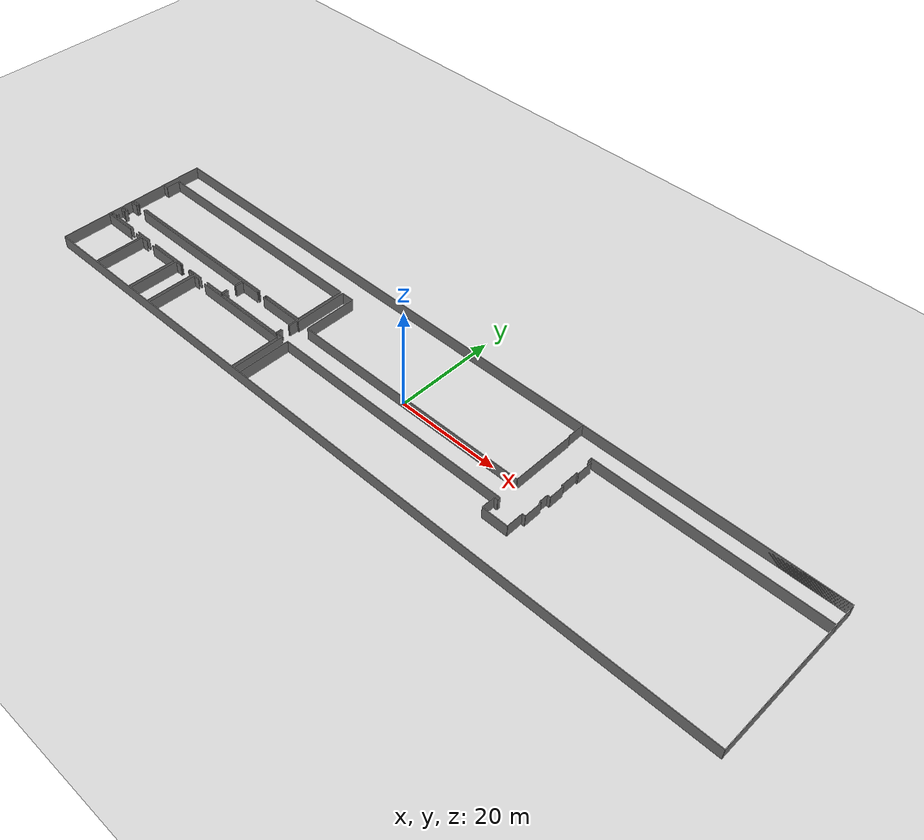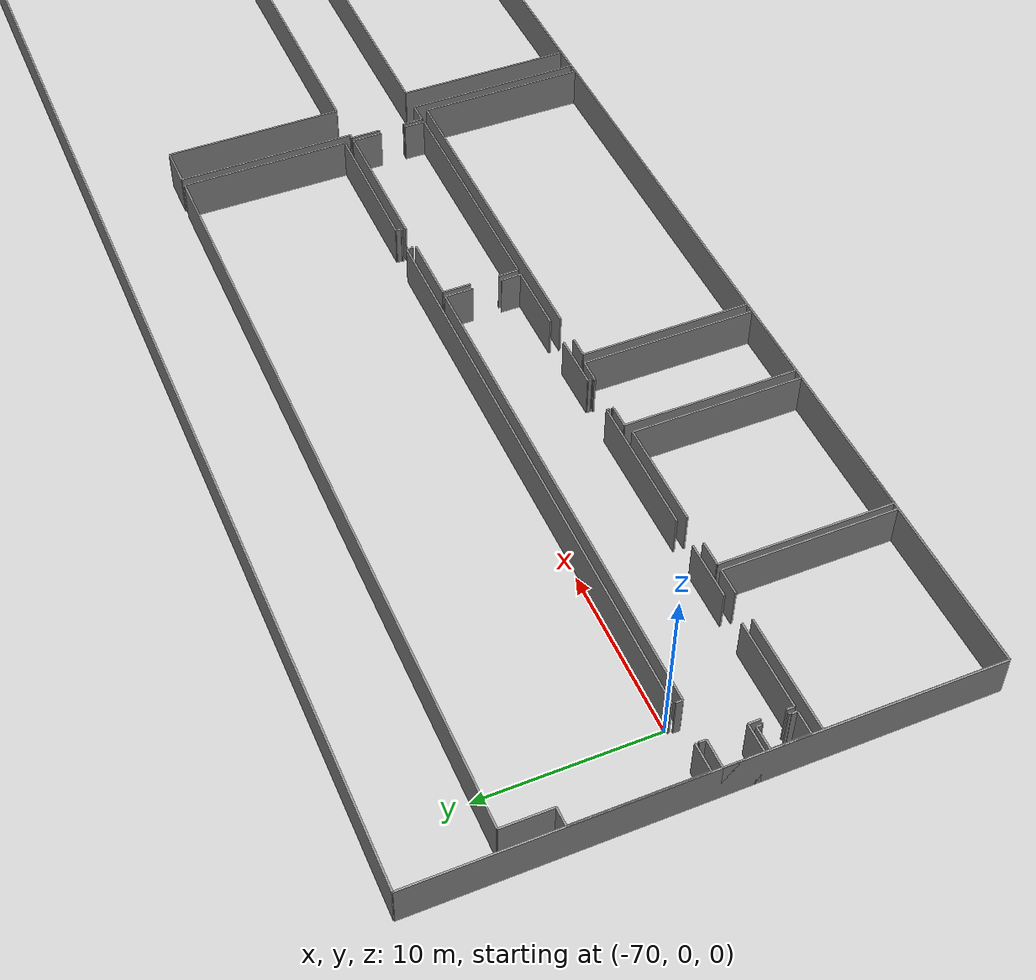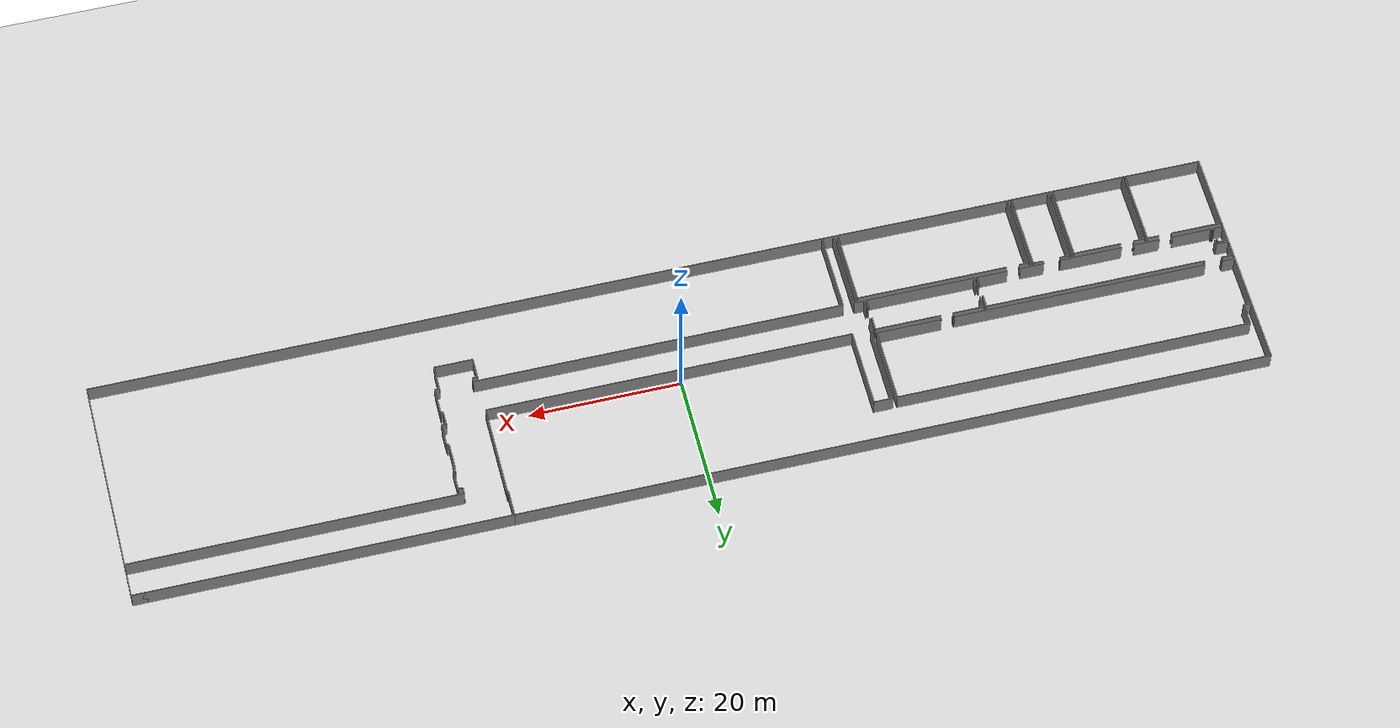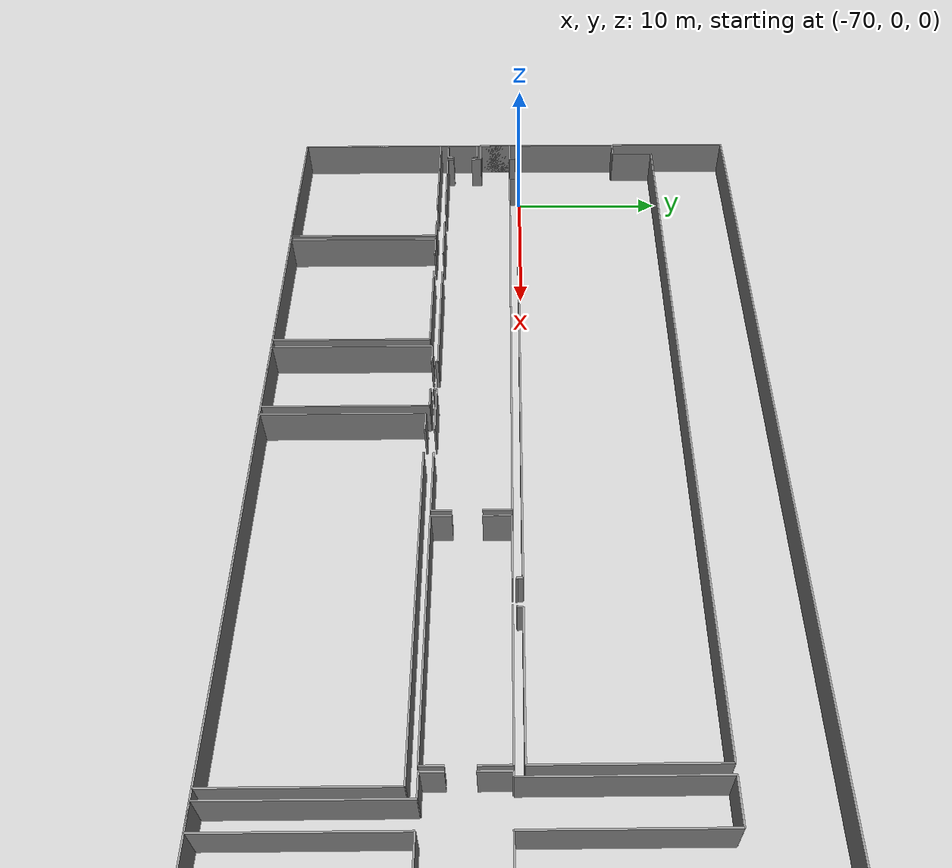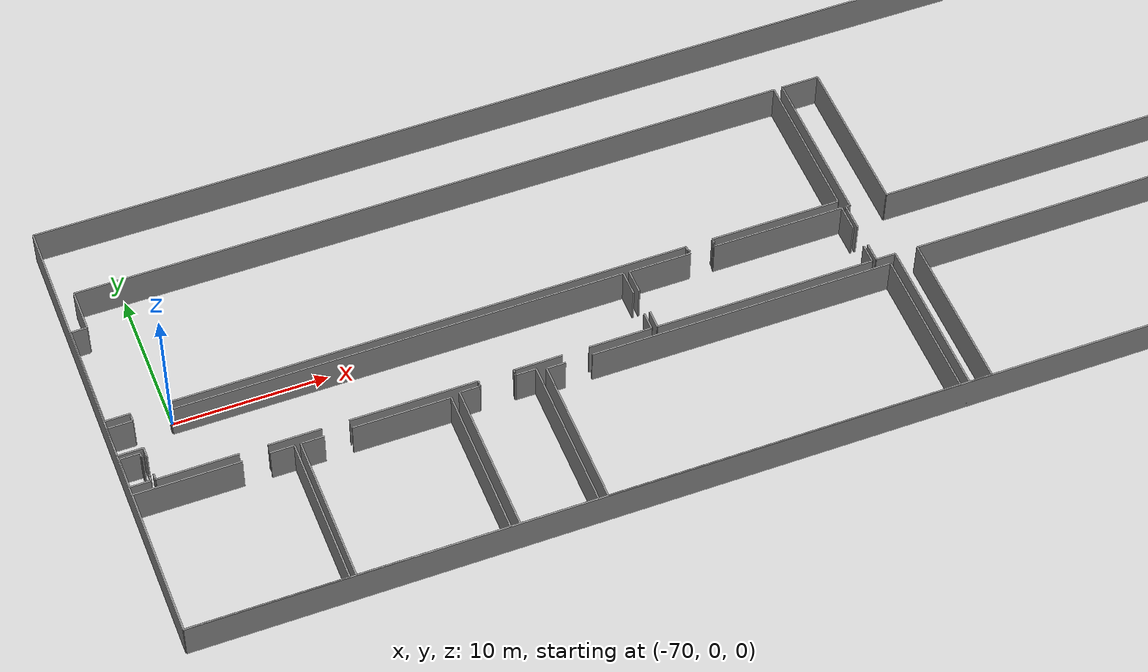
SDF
<sdf version="1.6">
  <world name="default">
    <light name="sun" type="directional">
      <cast_shadows>1</cast_shadows>
      <pose frame="">0 0 10 0 -0 0</pose>
      <diffuse>0.8 0.8 0.8 1</diffuse>
      <specular>0.1 0.1 0.1 1</specular>
      <attenuation>
        <range>1000</range>
        <constant>0.9</constant>
        <linear>0.01</linear>
        <quadratic>0.001</quadratic>
      </attenuation>
      <direction>-0.5 0.5 -1</direction>
    </light>
    <model name="ground_plane">
      <static>1</static>
      <link name="link">
        <collision name="collision">
          <geometry>
            <plane>
              <normal>0 0 1</normal>
              <size>100 100</size>
            </plane>
          </geometry>
          <surface>
            <friction>
              <ode>
                <mu>100</mu>
                <mu2>50</mu2>
              </ode>
              <torsional>
                <ode />
              </torsional>
            </friction>
            <contact>
              <ode />
            </contact>
            <bounce />
          </surface>
          <max_contacts>10</max_contacts>
        </collision>
        <visual name="visual">
          <cast_shadows>0</cast_shadows>
          <geometry>
            <plane>
              <normal>0 0 1</normal>
              <size>100 100</size>
            </plane>
          </geometry>
          <material>
            <script>
              <uri>file://media/materials/scripts/gazebo.material</uri>
              <name>Gazebo/Grey</name>
            </script>
          </material>
        </visual>
        <self_collide>0</self_collide>
        <kinematic>0</kinematic>
        <gravity>1</gravity>
      </link>
    </model>
    <gravity>0 0 -9.8</gravity>
    <magnetic_field>6e-06 2.3e-05 -4.2e-05</magnetic_field>
    <atmosphere type="adiabatic" />
    <physics default="0" name="default_physics" type="ode">
      <max_step_size>0.001</max_step_size>
      <real_time_factor>1</real_time_factor>
      <real_time_update_rate>1000</real_time_update_rate>
    </physics>
    <scene>
      <ambient>0.4 0.4 0.4 1</ambient>
      <background>0.7 0.7 0.7 1</background>
      <shadows>1</shadows>
    </scene>
    <spherical_coordinates>
      <surface_model>EARTH_WGS84</surface_model>
      <latitude_deg>0</latitude_deg>
      <longitude_deg>0</longitude_deg>
      <elevation>0</elevation>
      <heading_deg>0</heading_deg>
    </spherical_coordinates>
  <model name="50055637">
		<static>1</static>
		<link name="Wall_0">
			<collision name="Wall_0_Collision">
				<geometry>
					<box>
						<size>10.0771707856 0.1 2.5</size>
					</box>
				</geometry>
				<pose frame="">5.03858539281 0 1.25 0 0 0</pose>
			</collision>
			<visual name="Wall_0_Visual">
				<pose frame="">5.03858539281 0 1.25 0 0 0</pose>
				<geometry>
					<box>
						<size>10.0771707856 0.1 2.5</size>
					</box>
				</geometry>
				<material>
					<script>
						<uri>file://media/materials/scripts/gazebo.material</uri>
						<name>Gazebo/Grey</name>
					</script>
					<ambient>1 1 1 1</ambient>
				</material>
			</visual>
			<pose frame="">0.0217221470627 -31.2967867736 0 0 0 1.57079632679</pose>
		</link>
		<link name="Wall_1">
			<collision name="Wall_1_Collision">
				<geometry>
					<box>
						<size>6.82672459239 0.1 2.5</size>
					</box>
				</geometry>
				<pose frame="">3.4133622962 0 1.25 0 0 0</pose>
			</collision>
			<visual name="Wall_1_Visual">
				<pose frame="">3.4133622962 0 1.25 0 0 0</pose>
				<geometry>
					<box>
						<size>6.82672459239 0.1 2.5</size>
					</box>
				</geometry>
				<material>
					<script>
						<uri>file://media/materials/scripts/gazebo.material</uri>
						<name>Gazebo/Grey</name>
					</script>
					<ambient>1 1 1 1</ambient>
				</material>
			</visual>
			<pose frame="">0.0217221470627 -21.219615988 0 0 0 0.0</pose>
		</link>
		<link name="Wall_2">
			<collision name="Wall_2_Collision">
				<geometry>
					<box>
						<size>1.54836988624 0.1 2.5</size>
					</box>
				</geometry>
				<pose frame="">0.774184943122 0 1.25 0 0 0</pose>
			</collision>
			<visual name="Wall_2_Visual">
				<pose frame="">0.774184943122 0 1.25 0 0 0</pose>
				<geometry>
					<box>
						<size>1.54836988624 0.1 2.5</size>
					</box>
				</geometry>
				<material>
					<script>
						<uri>file://media/materials/scripts/gazebo.material</uri>
						<name>Gazebo/Grey</name>
					</script>
					<ambient>1 1 1 1</ambient>
				</material>
			</visual>
			<pose frame="">8.56690992931 -21.219615988 0 0 0 0.0</pose>
		</link>
		<link name="Wall_3">
			<collision name="Wall_3_Collision">
				<geometry>
					<box>
						<size>10.0830141702 0.1 2.5</size>
					</box>
				</geometry>
				<pose frame="">5.0415070851 0 1.25 0 0 0</pose>
			</collision>
			<visual name="Wall_3_Visual">
				<pose frame="">5.0415070851 0 1.25 0 0 0</pose>
				<geometry>
					<box>
						<size>10.0830141702 0.1 2.5</size>
					</box>
				</geometry>
				<material>
					<script>
						<uri>file://media/materials/scripts/gazebo.material</uri>
						<name>Gazebo/Grey</name>
					</script>
					<ambient>1 1 1 1</ambient>
				</material>
			</visual>
			<pose frame="">10.1152798156 -21.219615988 0 0 0 -1.57079632679</pose>
		</link>
		<link name="Wall_4">
			<collision name="Wall_4_Collision">
				<geometry>
					<box>
						<size>10.0935593599 0.1 2.5</size>
					</box>
				</geometry>
				<pose frame="">5.04677967996 0 1.25 0 0 0</pose>
			</collision>
			<visual name="Wall_4_Visual">
				<pose frame="">5.04677967996 0 1.25 0 0 0</pose>
				<geometry>
					<box>
						<size>10.0935593599 0.1 2.5</size>
					</box>
				</geometry>
				<material>
					<script>
						<uri>file://media/materials/scripts/gazebo.material</uri>
						<name>Gazebo/Grey</name>
					</script>
					<ambient>1 1 1 1</ambient>
				</material>
			</visual>
			<pose frame="">10.1152798156 -31.3026301582 0 0 0 3.14101373146</pose>
		</link>
		<link name="Wall_5">
			<collision name="Wall_5_Collision">
				<geometry>
					<box>
						<size>7.21988275122 0.1 2.5</size>
					</box>
				</geometry>
				<pose frame="">3.60994137561 0 1.25 0 0 0</pose>
			</collision>
			<visual name="Wall_5_Visual">
				<pose frame="">3.60994137561 0 1.25 0 0 0</pose>
				<geometry>
					<box>
						<size>7.21988275122 0.1 2.5</size>
					</box>
				</geometry>
				<material>
					<script>
						<uri>file://media/materials/scripts/gazebo.material</uri>
						<name>Gazebo/Grey</name>
					</script>
					<ambient>1 1 1 1</ambient>
				</material>
			</visual>
			<pose frame="">0.0287088025508 -15.4609604746 0 0 0 1.57079632679</pose>
		</link>
		<link name="Wall_6">
			<collision name="Wall_6_Collision">
				<geometry>
					<box>
						<size>1.0524443767 0.1 2.5</size>
					</box>
				</geometry>
				<pose frame="">0.526222188348 0 1.25 0 0 0</pose>
			</collision>
			<visual name="Wall_6_Visual">
				<pose frame="">0.526222188348 0 1.25 0 0 0</pose>
				<geometry>
					<box>
						<size>1.0524443767 0.1 2.5</size>
					</box>
				</geometry>
				<material>
					<script>
						<uri>file://media/materials/scripts/gazebo.material</uri>
						<name>Gazebo/Grey</name>
					</script>
					<ambient>1 1 1 1</ambient>
				</material>
			</visual>
			<pose frame="">0.0287088025508 -8.24107772337 0 0 0 0.0</pose>
		</link>
		<link name="Wall_7">
			<collision name="Wall_7_Collision">
				<geometry>
					<box>
						<size>2.86897480358 0.1 2.5</size>
					</box>
				</geometry>
				<pose frame="">1.43448740179 0 1.25 0 0 0</pose>
			</collision>
			<visual name="Wall_7_Visual">
				<pose frame="">1.43448740179 0 1.25 0 0 0</pose>
				<geometry>
					<box>
						<size>2.86897480358 0.1 2.5</size>
					</box>
				</geometry>
				<material>
					<script>
						<uri>file://media/materials/scripts/gazebo.material</uri>
						<name>Gazebo/Grey</name>
					</script>
					<ambient>1 1 1 1</ambient>
				</material>
			</visual>
			<pose frame="">1.08115317925 -8.24107772337 0 0 0 1.57079632679</pose>
		</link>
		<link name="Wall_8">
			<collision name="Wall_8_Collision">
				<geometry>
					<box>
						<size>47.1135585577 0.1 2.5</size>
					</box>
				</geometry>
				<pose frame="">23.5567792789 0 1.25 0 0 0</pose>
			</collision>
			<visual name="Wall_8_Visual">
				<pose frame="">23.5567792789 0 1.25 0 0 0</pose>
				<geometry>
					<box>
						<size>47.1135585577 0.1 2.5</size>
					</box>
				</geometry>
				<material>
					<script>
						<uri>file://media/materials/scripts/gazebo.material</uri>
						<name>Gazebo/Grey</name>
					</script>
					<ambient>1 1 1 1</ambient>
				</material>
			</visual>
			<pose frame="">1.08115317925 -5.37210291979 0 0 0 0.0</pose>
		</link>
		<link name="Wall_9">
			<collision name="Wall_9_Collision">
				<geometry>
					<box>
						<size>10.0919062772 0.1 2.5</size>
					</box>
				</geometry>
				<pose frame="">5.0459531386 0 1.25 0 0 0</pose>
			</collision>
			<visual name="Wall_9_Visual">
				<pose frame="">5.0459531386 0 1.25 0 0 0</pose>
				<geometry>
					<box>
						<size>10.0919062772 0.1 2.5</size>
					</box>
				</geometry>
				<material>
					<script>
						<uri>file://media/materials/scripts/gazebo.material</uri>
						<name>Gazebo/Grey</name>
					</script>
					<ambient>1 1 1 1</ambient>
				</material>
			</visual>
			<pose frame="">48.1947117369 -5.37210291979 0 0 0 -1.57079632679</pose>
		</link>
		<link name="Wall_10">
			<collision name="Wall_10_Collision">
				<geometry>
					<box>
						<size>8.60171617665 0.1 2.5</size>
					</box>
				</geometry>
				<pose frame="">4.30085808832 0 1.25 0 0 0</pose>
			</collision>
			<visual name="Wall_10_Visual">
				<pose frame="">4.30085808832 0 1.25 0 0 0</pose>
				<geometry>
					<box>
						<size>8.60171617665 0.1 2.5</size>
					</box>
				</geometry>
				<material>
					<script>
						<uri>file://media/materials/scripts/gazebo.material</uri>
						<name>Gazebo/Grey</name>
					</script>
					<ambient>1 1 1 1</ambient>
				</material>
			</visual>
			<pose frame="">48.1947117369 -15.464009197 0 0 0 3.14159265359</pose>
		</link>
		<link name="Wall_11">
			<collision name="Wall_11_Collision">
				<geometry>
					<box>
						<size>0.336629764423 0.1 2.5</size>
					</box>
				</geometry>
				<pose frame="">0.168314882211 0 1.25 0 0 0</pose>
			</collision>
			<visual name="Wall_11_Visual">
				<pose frame="">0.168314882211 0 1.25 0 0 0</pose>
				<geometry>
					<box>
						<size>0.336629764423 0.1 2.5</size>
					</box>
				</geometry>
				<material>
					<script>
						<uri>file://media/materials/scripts/gazebo.material</uri>
						<name>Gazebo/Grey</name>
					</script>
					<ambient>1 1 1 1</ambient>
				</material>
			</visual>
			<pose frame="">39.5929955603 -15.464009197 0 0 0 -1.57079632679</pose>
		</link>
		<link name="Wall_12">
			<collision name="Wall_12_Collision">
				<geometry>
					<box>
						<size>0.10479983232 0.1 2.5</size>
					</box>
				</geometry>
				<pose frame="">0.0523999161601 0 1.25 0 0 0</pose>
			</collision>
			<visual name="Wall_12_Visual">
				<pose frame="">0.0523999161601 0 1.25 0 0 0</pose>
				<geometry>
					<box>
						<size>0.10479983232 0.1 2.5</size>
					</box>
				</geometry>
				<material>
					<script>
						<uri>file://media/materials/scripts/gazebo.material</uri>
						<name>Gazebo/Grey</name>
					</script>
					<ambient>1 1 1 1</ambient>
				</material>
			</visual>
			<pose frame="">39.5929955603 -15.8006389614 0 0 0 3.14159265359</pose>
		</link>
		<link name="Wall_13">
			<collision name="Wall_13_Collision">
				<geometry>
					<box>
						<size>0.129189611478 0.1 2.5</size>
					</box>
				</geometry>
				<pose frame="">0.0645948057392 0 1.25 0 0 0</pose>
			</collision>
			<visual name="Wall_13_Visual">
				<pose frame="">0.0645948057392 0 1.25 0 0 0</pose>
				<geometry>
					<box>
						<size>0.129189611478 0.1 2.5</size>
					</box>
				</geometry>
				<material>
					<script>
						<uri>file://media/materials/scripts/gazebo.material</uri>
						<name>Gazebo/Grey</name>
					</script>
					<ambient>1 1 1 1</ambient>
				</material>
			</visual>
			<pose frame="">37.9441448651 -15.8006389614 0 0 0 3.14159265359</pose>
		</link>
		<link name="Wall_14">
			<collision name="Wall_14_Collision">
				<geometry>
					<box>
						<size>0.339805516917 0.1 2.5</size>
					</box>
				</geometry>
				<pose frame="">0.169902758459 0 1.25 0 0 0</pose>
			</collision>
			<visual name="Wall_14_Visual">
				<pose frame="">0.169902758459 0 1.25 0 0 0</pose>
				<geometry>
					<box>
						<size>0.339805516917 0.1 2.5</size>
					</box>
				</geometry>
				<material>
					<script>
						<uri>file://media/materials/scripts/gazebo.material</uri>
						<name>Gazebo/Grey</name>
					</script>
					<ambient>1 1 1 1</ambient>
				</material>
			</visual>
			<pose frame="">37.8149552536 -15.8006389614 0 0 0 1.57079632679</pose>
		</link>
		<link name="Wall_15">
			<collision name="Wall_15_Collision">
				<geometry>
					<box>
						<size>33.8066474851 0.1 2.5</size>
					</box>
				</geometry>
				<pose frame="">16.9033237426 0 1.25 0 0 0</pose>
			</collision>
			<visual name="Wall_15_Visual">
				<pose frame="">16.9033237426 0 1.25 0 0 0</pose>
				<geometry>
					<box>
						<size>33.8066474851 0.1 2.5</size>
					</box>
				</geometry>
				<material>
					<script>
						<uri>file://media/materials/scripts/gazebo.material</uri>
						<name>Gazebo/Grey</name>
					</script>
					<ambient>1 1 1 1</ambient>
				</material>
			</visual>
			<pose frame="">37.8149552536 -15.4608334445 0 0 0 3.14159265359</pose>
		</link>
		<link name="Wall_16">
			<collision name="Wall_16_Collision">
				<geometry>
					<box>
						<size>1.641101864 0.1 2.5</size>
					</box>
				</geometry>
				<pose frame="">0.820550932001 0 1.25 0 0 0</pose>
			</collision>
			<visual name="Wall_16_Visual">
				<pose frame="">0.820550932001 0 1.25 0 0 0</pose>
				<geometry>
					<box>
						<size>1.641101864 0.1 2.5</size>
					</box>
				</geometry>
				<material>
					<script>
						<uri>file://media/materials/scripts/gazebo.material</uri>
						<name>Gazebo/Grey</name>
					</script>
					<ambient>1 1 1 1</ambient>
				</material>
			</visual>
			<pose frame="">1.66981066164 -15.4608334445 0 0 0 -3.14151524822</pose>
		</link>
		<link name="Wall_17">
			<collision name="Wall_17_Collision">
				<geometry>
					<box>
						<size>2.1567170341 0.1 2.5</size>
					</box>
				</geometry>
				<pose frame="">1.07835851705 0 1.25 0 0 0</pose>
			</collision>
			<visual name="Wall_17_Visual">
				<pose frame="">1.07835851705 0 1.25 0 0 0</pose>
				<geometry>
					<box>
						<size>2.1567170341 0.1 2.5</size>
					</box>
				</geometry>
				<material>
					<script>
						<uri>file://media/materials/scripts/gazebo.material</uri>
						<name>Gazebo/Grey</name>
					</script>
					<ambient>1 1 1 1</ambient>
				</material>
			</visual>
			<pose frame="">0.0284547423512 -20.6284179036 0 0 0 1.57079632679</pose>
		</link>
		<link name="Wall_18">
			<collision name="Wall_18_Collision">
				<geometry>
					<box>
						<size>1.32073194743 0.1 2.5</size>
					</box>
				</geometry>
				<pose frame="">0.660365973717 0 1.25 0 0 0</pose>
			</collision>
			<visual name="Wall_18_Visual">
				<pose frame="">0.660365973717 0 1.25 0 0 0</pose>
				<geometry>
					<box>
						<size>1.32073194743 0.1 2.5</size>
					</box>
				</geometry>
				<material>
					<script>
						<uri>file://media/materials/scripts/gazebo.material</uri>
						<name>Gazebo/Grey</name>
					</script>
					<ambient>1 1 1 1</ambient>
				</material>
			</visual>
			<pose frame="">0.0284547423512 -18.4717008695 0 0 0 0.0</pose>
		</link>
		<link name="Wall_19">
			<collision name="Wall_19_Collision">
				<geometry>
					<box>
						<size>0.275401256328 0.1 2.5</size>
					</box>
				</geometry>
				<pose frame="">0.137700628164 0 1.25 0 0 0</pose>
			</collision>
			<visual name="Wall_19_Visual">
				<pose frame="">0.137700628164 0 1.25 0 0 0</pose>
				<geometry>
					<box>
						<size>0.275401256328 0.1 2.5</size>
					</box>
				</geometry>
				<material>
					<script>
						<uri>file://media/materials/scripts/gazebo.material</uri>
						<name>Gazebo/Grey</name>
					</script>
					<ambient>1 1 1 1</ambient>
				</material>
			</visual>
			<pose frame="">1.34918668979 -18.4717008695 0 0 0 -1.57079632679</pose>
		</link>
		<link name="Wall_20">
			<collision name="Wall_20_Collision">
				<geometry>
					<box>
						<size>0.0569094847024 0.1 2.5</size>
					</box>
				</geometry>
				<pose frame="">0.0284547423512 0 1.25 0 0 0</pose>
			</collision>
			<visual name="Wall_20_Visual">
				<pose frame="">0.0284547423512 0 1.25 0 0 0</pose>
				<geometry>
					<box>
						<size>0.0569094847024 0.1 2.5</size>
					</box>
				</geometry>
				<material>
					<script>
						<uri>file://media/materials/scripts/gazebo.material</uri>
						<name>Gazebo/Grey</name>
					</script>
					<ambient>1 1 1 1</ambient>
				</material>
			</visual>
			<pose frame="">1.34918668979 -18.7471021258 0 0 0 0.0</pose>
		</link>
		<link name="Wall_21">
			<collision name="Wall_21_Collision">
				<geometry>
					<box>
						<size>0.0901913708453 0.1 2.5</size>
					</box>
				</geometry>
				<pose frame="">0.0450956854227 0 1.25 0 0 0</pose>
			</collision>
			<visual name="Wall_21_Visual">
				<pose frame="">0.0450956854227 0 1.25 0 0 0</pose>
				<geometry>
					<box>
						<size>0.0901913708453 0.1 2.5</size>
					</box>
				</geometry>
				<material>
					<script>
						<uri>file://media/materials/scripts/gazebo.material</uri>
						<name>Gazebo/Grey</name>
					</script>
					<ambient>1 1 1 1</ambient>
				</material>
			</visual>
			<pose frame="">1.40609617449 -18.7471021258 0 0 0 -1.57079632679</pose>
		</link>
		<link name="Wall_22">
			<collision name="Wall_22_Collision">
				<geometry>
					<box>
						<size>0.12245701619 0.1 2.5</size>
					</box>
				</geometry>
				<pose frame="">0.061228508095 0 1.25 0 0 0</pose>
			</collision>
			<visual name="Wall_22_Visual">
				<pose frame="">0.061228508095 0 1.25 0 0 0</pose>
				<geometry>
					<box>
						<size>0.12245701619 0.1 2.5</size>
					</box>
				</geometry>
				<material>
					<script>
						<uri>file://media/materials/scripts/gazebo.material</uri>
						<name>Gazebo/Grey</name>
					</script>
					<ambient>1 1 1 1</ambient>
				</material>
			</visual>
			<pose frame="">1.40609617449 -20.1772069892 0 0 0 -1.57079632679</pose>
		</link>
		<link name="Wall_23">
			<collision name="Wall_23_Collision">
				<geometry>
					<box>
						<size>0.0459848961211 0.1 2.5</size>
					</box>
				</geometry>
				<pose frame="">0.0229924480606 0 1.25 0 0 0</pose>
			</collision>
			<visual name="Wall_23_Visual">
				<pose frame="">0.0229924480606 0 1.25 0 0 0</pose>
				<geometry>
					<box>
						<size>0.0459848961211 0.1 2.5</size>
					</box>
				</geometry>
				<material>
					<script>
						<uri>file://media/materials/scripts/gazebo.material</uri>
						<name>Gazebo/Grey</name>
					</script>
					<ambient>1 1 1 1</ambient>
				</material>
			</visual>
			<pose frame="">1.40609617449 -20.2996640054 0 0 0 3.14159265359</pose>
		</link>
		<link name="Wall_24">
			<collision name="Wall_24_Collision">
				<geometry>
					<box>
						<size>0.332818861429 0.1 2.5</size>
					</box>
				</geometry>
				<pose frame="">0.166409430715 0 1.25 0 0 0</pose>
			</collision>
			<visual name="Wall_24_Visual">
				<pose frame="">0.166409430715 0 1.25 0 0 0</pose>
				<geometry>
					<box>
						<size>0.332818861429 0.1 2.5</size>
					</box>
				</geometry>
				<material>
					<script>
						<uri>file://media/materials/scripts/gazebo.material</uri>
						<name>Gazebo/Grey</name>
					</script>
					<ambient>1 1 1 1</ambient>
				</material>
			</visual>
			<pose frame="">1.36011127837 -20.2996640054 0 0 0 -1.57079632679</pose>
		</link>
		<link name="Wall_25">
			<collision name="Wall_25_Collision">
				<geometry>
					<box>
						<size>1.33166274028 0.1 2.5</size>
					</box>
				</geometry>
				<pose frame="">0.665831370138 0 1.25 0 0 0</pose>
			</collision>
			<visual name="Wall_25_Visual">
				<pose frame="">0.665831370138 0 1.25 0 0 0</pose>
				<geometry>
					<box>
						<size>1.33166274028 0.1 2.5</size>
					</box>
				</geometry>
				<material>
					<script>
						<uri>file://media/materials/scripts/gazebo.material</uri>
						<name>Gazebo/Grey</name>
					</script>
					<ambient>1 1 1 1</ambient>
				</material>
			</visual>
			<pose frame="">1.36011127837 -20.6324828668 0 0 0 3.13854010178</pose>
		</link>
		<link name="Wall_26">
			<collision name="Wall_26_Collision">
				<geometry>
					<box>
						<size>10.0817438692 0.1 2.5</size>
					</box>
				</geometry>
				<pose frame="">5.0408719346 0 1.25 0 0 0</pose>
			</collision>
			<visual name="Wall_26_Visual">
				<pose frame="">5.0408719346 0 1.25 0 0 0</pose>
				<geometry>
					<box>
						<size>10.0817438692 0.1 2.5</size>
					</box>
				</geometry>
				<material>
					<script>
						<uri>file://media/materials/scripts/gazebo.material</uri>
						<name>Gazebo/Grey</name>
					</script>
					<ambient>1 1 1 1</ambient>
				</material>
			</visual>
			<pose frame="">10.5067865831 -31.2975489542 0 0 0 1.57079632679</pose>
		</link>
		<link name="Wall_27">
			<collision name="Wall_27_Collision">
				<geometry>
					<box>
						<size>1.48917385975 0.1 2.5</size>
					</box>
				</geometry>
				<pose frame="">0.744586929873 0 1.25 0 0 0</pose>
			</collision>
			<visual name="Wall_27_Visual">
				<pose frame="">0.744586929873 0 1.25 0 0 0</pose>
				<geometry>
					<box>
						<size>1.48917385975 0.1 2.5</size>
					</box>
				</geometry>
				<material>
					<script>
						<uri>file://media/materials/scripts/gazebo.material</uri>
						<name>Gazebo/Grey</name>
					</script>
					<ambient>1 1 1 1</ambient>
				</material>
			</visual>
			<pose frame="">10.5067865831 -21.215805085 0 0 0 0.0</pose>
		</link>
		<link name="Wall_28">
			<collision name="Wall_28_Collision">
				<geometry>
					<box>
						<size>6.33295859454 0.1 2.5</size>
					</box>
				</geometry>
				<pose frame="">3.16647929727 0 1.25 0 0 0</pose>
			</collision>
			<visual name="Wall_28_Visual">
				<pose frame="">3.16647929727 0 1.25 0 0 0</pose>
				<geometry>
					<box>
						<size>6.33295859454 0.1 2.5</size>
					</box>
				</geometry>
				<material>
					<script>
						<uri>file://media/materials/scripts/gazebo.material</uri>
						<name>Gazebo/Grey</name>
					</script>
					<ambient>1 1 1 1</ambient>
				</material>
			</visual>
			<pose frame="">13.745418977 -21.215805085 0 0 0 0.0</pose>
		</link>
		<link name="Wall_29">
			<collision name="Wall_29_Collision">
				<geometry>
					<box>
						<size>10.0950820297 0.1 2.5</size>
					</box>
				</geometry>
				<pose frame="">5.04754101484 0 1.25 0 0 0</pose>
			</collision>
			<visual name="Wall_29_Visual">
				<pose frame="">5.04754101484 0 1.25 0 0 0</pose>
				<geometry>
					<box>
						<size>10.0950820297 0.1 2.5</size>
					</box>
				</geometry>
				<material>
					<script>
						<uri>file://media/materials/scripts/gazebo.material</uri>
						<name>Gazebo/Grey</name>
					</script>
					<ambient>1 1 1 1</ambient>
				</material>
			</visual>
			<pose frame="">20.0783775716 -21.215805085 0 0 0 -1.57079632679</pose>
		</link>
		<link name="Wall_30">
			<collision name="Wall_30_Collision">
				<geometry>
					<box>
						<size>9.57160028195 0.1 2.5</size>
					</box>
				</geometry>
				<pose frame="">4.78580014097 0 1.25 0 0 0</pose>
			</collision>
			<visual name="Wall_30_Visual">
				<pose frame="">4.78580014097 0 1.25 0 0 0</pose>
				<geometry>
					<box>
						<size>9.57160028195 0.1 2.5</size>
					</box>
				</geometry>
				<material>
					<script>
						<uri>file://media/materials/scripts/gazebo.material</uri>
						<name>Gazebo/Grey</name>
					</script>
					<ambient>1 1 1 1</ambient>
				</material>
			</visual>
			<pose frame="">20.0783775716 -31.3108871147 0 0 0 3.14019913898</pose>
		</link>
		<link name="Wall_31">
			<collision name="Wall_31_Collision">
				<geometry>
					<box>
						<size>10.272416049 0.1 2.5</size>
					</box>
				</geometry>
				<pose frame="">5.13620802449 0 1.25 0 0 0</pose>
			</collision>
			<visual name="Wall_31_Visual">
				<pose frame="">5.13620802449 0 1.25 0 0 0</pose>
				<geometry>
					<box>
						<size>10.272416049 0.1 2.5</size>
					</box>
				</geometry>
				<material>
					<script>
						<uri>file://media/materials/scripts/gazebo.material</uri>
						<name>Gazebo/Grey</name>
					</script>
					<ambient>1 1 1 1</ambient>
				</material>
			</visual>
			<pose frame="">20.6778326124 -31.3017409475 0 0 0 1.57079632679</pose>
		</link>
		<link name="Wall_32">
			<collision name="Wall_32_Collision">
				<geometry>
					<box>
						<size>1.31158578025 0.1 2.5</size>
					</box>
				</geometry>
				<pose frame="">0.655792890125 0 1.25 0 0 0</pose>
			</collision>
			<visual name="Wall_32_Visual">
				<pose frame="">0.655792890125 0 1.25 0 0 0</pose>
				<geometry>
					<box>
						<size>1.31158578025 0.1 2.5</size>
					</box>
				</geometry>
				<material>
					<script>
						<uri>file://media/materials/scripts/gazebo.material</uri>
						<name>Gazebo/Grey</name>
					</script>
					<ambient>1 1 1 1</ambient>
				</material>
			</visual>
			<pose frame="">20.6778326124 -21.0293248985 0 0 0 0.0</pose>
		</link>
		<link name="Wall_33">
			<collision name="Wall_33_Collision">
				<geometry>
					<box>
						<size>0.0325197055442 0.1 2.5</size>
					</box>
				</geometry>
				<pose frame="">0.0162598527721 0 1.25 0 0 0</pose>
			</collision>
			<visual name="Wall_33_Visual">
				<pose frame="">0.0162598527721 0 1.25 0 0 0</pose>
				<geometry>
					<box>
						<size>0.0325197055442 0.1 2.5</size>
					</box>
				</geometry>
				<material>
					<script>
						<uri>file://media/materials/scripts/gazebo.material</uri>
						<name>Gazebo/Grey</name>
					</script>
					<ambient>1 1 1 1</ambient>
				</material>
			</visual>
			<pose frame="">21.9894183927 -21.0293248985 0 0 0 1.57079632679</pose>
		</link>
		<link name="Wall_34">
			<collision name="Wall_34_Collision">
				<geometry>
					<box>
						<size>0.0829506551577 0.1 2.5</size>
					</box>
				</geometry>
				<pose frame="">0.0414753275789 0 1.25 0 0 0</pose>
			</collision>
			<visual name="Wall_34_Visual">
				<pose frame="">0.0414753275789 0 1.25 0 0 0</pose>
				<geometry>
					<box>
						<size>0.0829506551577 0.1 2.5</size>
					</box>
				</geometry>
				<material>
					<script>
						<uri>file://media/materials/scripts/gazebo.material</uri>
						<name>Gazebo/Grey</name>
					</script>
					<ambient>1 1 1 1</ambient>
				</material>
			</visual>
			<pose frame="">21.9894183927 -20.996805193 0 0 0 0.0</pose>
		</link>
		<link name="Wall_35">
			<collision name="Wall_35_Collision">
				<geometry>
					<box>
						<size>0.111913517908 0.1 2.5</size>
					</box>
				</geometry>
				<pose frame="">0.055956758954 0 1.25 0 0 0</pose>
			</collision>
			<visual name="Wall_35_Visual">
				<pose frame="">0.055956758954 0 1.25 0 0 0</pose>
				<geometry>
					<box>
						<size>0.111913517908 0.1 2.5</size>
					</box>
				</geometry>
				<material>
					<script>
						<uri>file://media/materials/scripts/gazebo.material</uri>
						<name>Gazebo/Grey</name>
					</script>
					<ambient>1 1 1 1</ambient>
				</material>
			</visual>
			<pose frame="">24.2489027775 -20.996805193 0 0 0 0.0</pose>
		</link>
		<link name="Wall_36">
			<collision name="Wall_36_Collision">
				<geometry>
					<box>
						<size>0.0199437256658 0.1 2.5</size>
					</box>
				</geometry>
				<pose frame="">0.0099718628329 0 1.25 0 0 0</pose>
			</collision>
			<visual name="Wall_36_Visual">
				<pose frame="">0.0099718628329 0 1.25 0 0 0</pose>
				<geometry>
					<box>
						<size>0.0199437256658 0.1 2.5</size>
					</box>
				</geometry>
				<material>
					<script>
						<uri>file://media/materials/scripts/gazebo.material</uri>
						<name>Gazebo/Grey</name>
					</script>
					<ambient>1 1 1 1</ambient>
				</material>
			</visual>
			<pose frame="">24.3608162954 -20.996805193 0 0 0 -1.57079632679</pose>
		</link>
		<link name="Wall_37">
			<collision name="Wall_37_Collision">
				<geometry>
					<box>
						<size>1.283258068 0.1 2.5</size>
					</box>
				</geometry>
				<pose frame="">0.641629034 0 1.25 0 0 0</pose>
			</collision>
			<visual name="Wall_37_Visual">
				<pose frame="">0.641629034 0 1.25 0 0 0</pose>
				<geometry>
					<box>
						<size>1.283258068 0.1 2.5</size>
					</box>
				</geometry>
				<material>
					<script>
						<uri>file://media/materials/scripts/gazebo.material</uri>
						<name>Gazebo/Grey</name>
					</script>
					<ambient>1 1 1 1</ambient>
				</material>
			</visual>
			<pose frame="">24.3608162954 -21.0167489187 0 0 0 0.0</pose>
		</link>
		<link name="Wall_38">
			<collision name="Wall_38_Collision">
				<geometry>
					<box>
						<size>10.2898191727 0.1 2.5</size>
					</box>
				</geometry>
				<pose frame="">5.14490958633 0 1.25 0 0 0</pose>
			</collision>
			<visual name="Wall_38_Visual">
				<pose frame="">5.14490958633 0 1.25 0 0 0</pose>
				<geometry>
					<box>
						<size>10.2898191727 0.1 2.5</size>
					</box>
				</geometry>
				<material>
					<script>
						<uri>file://media/materials/scripts/gazebo.material</uri>
						<name>Gazebo/Grey</name>
					</script>
					<ambient>1 1 1 1</ambient>
				</material>
			</visual>
			<pose frame="">25.6440743634 -21.0167489187 0 0 0 -1.57079632679</pose>
		</link>
		<link name="Wall_39">
			<collision name="Wall_39_Collision">
				<geometry>
					<box>
						<size>4.96624409695 0.1 2.5</size>
					</box>
				</geometry>
				<pose frame="">2.48312204848 0 1.25 0 0 0</pose>
			</collision>
			<visual name="Wall_39_Visual">
				<pose frame="">2.48312204848 0 1.25 0 0 0</pose>
				<geometry>
					<box>
						<size>4.96624409695 0.1 2.5</size>
					</box>
				</geometry>
				<material>
					<script>
						<uri>file://media/materials/scripts/gazebo.material</uri>
						<name>Gazebo/Grey</name>
					</script>
					<ambient>1 1 1 1</ambient>
				</material>
			</visual>
			<pose frame="">25.6440743634 -31.3065680913 0 0 0 3.14062066259</pose>
		</link>
		<link name="Wall_40">
			<collision name="Wall_40_Collision">
				<geometry>
					<box>
						<size>10.0747572137 0.1 2.5</size>
					</box>
				</geometry>
				<pose frame="">5.03737860686 0 1.25 0 0 0</pose>
			</collision>
			<visual name="Wall_40_Visual">
				<pose frame="">5.03737860686 0 1.25 0 0 0</pose>
				<geometry>
					<box>
						<size>10.0747572137 0.1 2.5</size>
					</box>
				</geometry>
				<material>
					<script>
						<uri>file://media/materials/scripts/gazebo.material</uri>
						<name>Gazebo/Grey</name>
					</script>
					<ambient>1 1 1 1</ambient>
				</material>
			</visual>
			<pose frame="">26.2445456451 -31.2989462853 0 0 0 1.57079632679</pose>
		</link>
		<link name="Wall_41">
			<collision name="Wall_41_Collision">
				<geometry>
					<box>
						<size>1.23803535248 0.1 2.5</size>
					</box>
				</geometry>
				<pose frame="">0.619017676238 0 1.25 0 0 0</pose>
			</collision>
			<visual name="Wall_41_Visual">
				<pose frame="">0.619017676238 0 1.25 0 0 0</pose>
				<geometry>
					<box>
						<size>1.23803535248 0.1 2.5</size>
					</box>
				</geometry>
				<material>
					<script>
						<uri>file://media/materials/scripts/gazebo.material</uri>
						<name>Gazebo/Grey</name>
					</script>
					<ambient>1 1 1 1</ambient>
				</material>
			</visual>
			<pose frame="">26.2445456451 -21.2241890716 0 0 0 0.0</pose>
		</link>
		<link name="Wall_42">
			<collision name="Wall_42_Collision">
				<geometry>
					<box>
						<size>19.9673532644 0.1 2.5</size>
					</box>
				</geometry>
				<pose frame="">9.98367663218 0 1.25 0 0 0</pose>
			</collision>
			<visual name="Wall_42_Visual">
				<pose frame="">9.98367663218 0 1.25 0 0 0</pose>
				<geometry>
					<box>
						<size>19.9673532644 0.1 2.5</size>
					</box>
				</geometry>
				<material>
					<script>
						<uri>file://media/materials/scripts/gazebo.material</uri>
						<name>Gazebo/Grey</name>
					</script>
					<ambient>1 1 1 1</ambient>
				</material>
			</visual>
			<pose frame="">29.2199716723 -21.2241890716 0 0 0 0.0</pose>
		</link>
		<link name="Wall_43">
			<collision name="Wall_43_Collision">
				<geometry>
					<box>
						<size>10.0823790197 0.1 2.5</size>
					</box>
				</geometry>
				<pose frame="">5.04118950985 0 1.25 0 0 0</pose>
			</collision>
			<visual name="Wall_43_Visual">
				<pose frame="">5.04118950985 0 1.25 0 0 0</pose>
				<geometry>
					<box>
						<size>10.0823790197 0.1 2.5</size>
					</box>
				</geometry>
				<material>
					<script>
						<uri>file://media/materials/scripts/gazebo.material</uri>
						<name>Gazebo/Grey</name>
					</script>
					<ambient>1 1 1 1</ambient>
				</material>
			</visual>
			<pose frame="">49.1873249366 -21.2241890716 0 0 0 -1.57079632679</pose>
		</link>
		<link name="Wall_44">
			<collision name="Wall_44_Collision">
				<geometry>
					<box>
						<size>22.9427805576 0.1 2.5</size>
					</box>
				</geometry>
				<pose frame="">11.4713902788 0 1.25 0 0 0</pose>
			</collision>
			<visual name="Wall_44_Visual">
				<pose frame="">11.4713902788 0 1.25 0 0 0</pose>
				<geometry>
					<box>
						<size>22.9427805576 0.1 2.5</size>
					</box>
				</geometry>
				<material>
					<script>
						<uri>file://media/materials/scripts/gazebo.material</uri>
						<name>Gazebo/Grey</name>
					</script>
					<ambient>1 1 1 1</ambient>
				</material>
			</visual>
			<pose frame="">49.1873249366 -31.3065680913 0 0 0 3.14126044424</pose>
		</link>
		<link name="Wall_45">
			<collision name="Wall_45_Collision">
				<geometry>
					<box>
						<size>2.1560818836 0.1 2.5</size>
					</box>
				</geometry>
				<pose frame="">1.0780409418 0 1.25 0 0 0</pose>
			</collision>
			<visual name="Wall_45_Visual">
				<pose frame="">1.0780409418 0 1.25 0 0 0</pose>
				<geometry>
					<box>
						<size>2.1560818836 0.1 2.5</size>
					</box>
				</geometry>
				<material>
					<script>
						<uri>file://media/materials/scripts/gazebo.material</uri>
						<name>Gazebo/Grey</name>
					</script>
					<ambient>1 1 1 1</ambient>
				</material>
			</visual>
			<pose frame="">0.0 -18.1799127303 0 0 0 1.57079632679</pose>
		</link>
		<link name="Wall_46">
			<collision name="Wall_46_Collision">
				<geometry>
					<box>
						<size>1.62928805981 0.1 2.5</size>
					</box>
				</geometry>
				<pose frame="">0.814644029903 0 1.25 0 0 0</pose>
			</collision>
			<visual name="Wall_46_Visual">
				<pose frame="">0.814644029903 0 1.25 0 0 0</pose>
				<geometry>
					<box>
						<size>1.62928805981 0.1 2.5</size>
					</box>
				</geometry>
				<material>
					<script>
						<uri>file://media/materials/scripts/gazebo.material</uri>
						<name>Gazebo/Grey</name>
					</script>
					<ambient>1 1 1 1</ambient>
				</material>
			</visual>
			<pose frame="">0.0 -16.0238308467 0 0 0 0.0</pose>
		</link>
		<link name="Wall_47">
			<collision name="Wall_47_Collision">
				<geometry>
					<box>
						<size>0.379947028448 0.1 2.5</size>
					</box>
				</geometry>
				<pose frame="">0.189973514224 0 1.25 0 0 0</pose>
			</collision>
			<visual name="Wall_47_Visual">
				<pose frame="">0.189973514224 0 1.25 0 0 0</pose>
				<geometry>
					<box>
						<size>0.379947028448 0.1 2.5</size>
					</box>
				</geometry>
				<material>
					<script>
						<uri>file://media/materials/scripts/gazebo.material</uri>
						<name>Gazebo/Grey</name>
					</script>
					<ambient>1 1 1 1</ambient>
				</material>
			</visual>
			<pose frame="">1.62928805981 -16.0238308467 0 0 0 1.57079632679</pose>
		</link>
		<link name="Wall_48">
			<collision name="Wall_48_Collision">
				<geometry>
					<box>
						<size>0.0308683142471 0.1 2.5</size>
					</box>
				</geometry>
				<pose frame="">0.0154341571235 0 1.25 0 0 0</pose>
			</collision>
			<visual name="Wall_48_Visual">
				<pose frame="">0.0154341571235 0 1.25 0 0 0</pose>
				<geometry>
					<box>
						<size>0.0308683142471 0.1 2.5</size>
					</box>
				</geometry>
				<material>
					<script>
						<uri>file://media/materials/scripts/gazebo.material</uri>
						<name>Gazebo/Grey</name>
					</script>
					<ambient>1 1 1 1</ambient>
				</material>
			</visual>
			<pose frame="">1.62928805981 -15.6438838183 0 0 0 0.0</pose>
		</link>
		<link name="Wall_49">
			<collision name="Wall_49_Collision">
				<geometry>
					<box>
						<size>0.369911650566 0.1 2.5</size>
					</box>
				</geometry>
				<pose frame="">0.184955825283 0 1.25 0 0 0</pose>
			</collision>
			<visual name="Wall_49_Visual">
				<pose frame="">0.184955825283 0 1.25 0 0 0</pose>
				<geometry>
					<box>
						<size>0.369911650566 0.1 2.5</size>
					</box>
				</geometry>
				<material>
					<script>
						<uri>file://media/materials/scripts/gazebo.material</uri>
						<name>Gazebo/Grey</name>
					</script>
					<ambient>1 1 1 1</ambient>
				</material>
			</visual>
			<pose frame="">3.98252065827 -15.6438838183 0 0 0 -1.57079632679</pose>
		</link>
		<link name="Wall_50">
			<collision name="Wall_50_Collision">
				<geometry>
					<box>
						<size>29.3934947886 0.1 2.5</size>
					</box>
				</geometry>
				<pose frame="">14.6967473943 0 1.25 0 0 0</pose>
			</collision>
			<visual name="Wall_50_Visual">
				<pose frame="">14.6967473943 0 1.25 0 0 0</pose>
				<geometry>
					<box>
						<size>29.3934947886 0.1 2.5</size>
					</box>
				</geometry>
				<material>
					<script>
						<uri>file://media/materials/scripts/gazebo.material</uri>
						<name>Gazebo/Grey</name>
					</script>
					<ambient>1 1 1 1</ambient>
				</material>
			</visual>
			<pose frame="">3.98252065827 -16.0137954688 0 0 0 0.0</pose>
		</link>
		<link name="Wall_51">
			<collision name="Wall_51_Collision">
				<geometry>
					<box>
						<size>1.68060822012 0.1 2.5</size>
					</box>
				</geometry>
				<pose frame="">0.840304110059 0 1.25 0 0 0</pose>
			</collision>
			<visual name="Wall_51_Visual">
				<pose frame="">0.840304110059 0 1.25 0 0 0</pose>
				<geometry>
					<box>
						<size>1.68060822012 0.1 2.5</size>
					</box>
				</geometry>
				<material>
					<script>
						<uri>file://media/materials/scripts/gazebo.material</uri>
						<name>Gazebo/Grey</name>
					</script>
					<ambient>1 1 1 1</ambient>
				</material>
			</visual>
			<pose frame="">33.3760154469 -16.0137954688 0 0 0 -1.57079632679</pose>
		</link>
		<link name="Wall_52">
			<collision name="Wall_52_Collision">
				<geometry>
					<box>
						<size>1.20056147304 0.1 2.5</size>
					</box>
				</geometry>
				<pose frame="">0.600280736521 0 1.25 0 0 0</pose>
			</collision>
			<visual name="Wall_52_Visual">
				<pose frame="">0.600280736521 0 1.25 0 0 0</pose>
				<geometry>
					<box>
						<size>1.20056147304 0.1 2.5</size>
					</box>
				</geometry>
				<material>
					<script>
						<uri>file://media/materials/scripts/gazebo.material</uri>
						<name>Gazebo/Grey</name>
					</script>
					<ambient>1 1 1 1</ambient>
				</material>
			</visual>
			<pose frame="">33.3760154469 -19.4297618821 0 0 0 -1.57079632679</pose>
		</link>
		<link name="Wall_53">
			<collision name="Wall_53_Collision">
				<geometry>
					<box>
						<size>4.12911339342 0.1 2.5</size>
					</box>
				</geometry>
				<pose frame="">2.06455669671 0 1.25 0 0 0</pose>
			</collision>
			<visual name="Wall_53_Visual">
				<pose frame="">2.06455669671 0 1.25 0 0 0</pose>
				<geometry>
					<box>
						<size>4.12911339342 0.1 2.5</size>
					</box>
				</geometry>
				<material>
					<script>
						<uri>file://media/materials/scripts/gazebo.material</uri>
						<name>Gazebo/Grey</name>
					</script>
					<ambient>1 1 1 1</ambient>
				</material>
			</visual>
			<pose frame="">33.3760154469 -20.6303233551 0 0 0 3.14159265359</pose>
		</link>
		<link name="Wall_54">
			<collision name="Wall_54_Collision">
				<geometry>
					<box>
						<size>3.16546305647 0.1 2.5</size>
					</box>
				</geometry>
				<pose frame="">1.58273152824 0 1.25 0 0 0</pose>
			</collision>
			<visual name="Wall_54_Visual">
				<pose frame="">1.58273152824 0 1.25 0 0 0</pose>
				<geometry>
					<box>
						<size>3.16546305647 0.1 2.5</size>
					</box>
				</geometry>
				<material>
					<script>
						<uri>file://media/materials/scripts/gazebo.material</uri>
						<name>Gazebo/Grey</name>
					</script>
					<ambient>1 1 1 1</ambient>
				</material>
			</visual>
			<pose frame="">27.5081140476 -20.6303233551 0 0 0 3.14159265359</pose>
		</link>
		<link name="Wall_55">
			<collision name="Wall_55_Collision">
				<geometry>
					<box>
						<size>0.183558494185 0.1 2.5</size>
					</box>
				</geometry>
				<pose frame="">0.0917792470926 0 1.25 0 0 0</pose>
			</collision>
			<visual name="Wall_55_Visual">
				<pose frame="">0.0917792470926 0 1.25 0 0 0</pose>
				<geometry>
					<box>
						<size>0.183558494185 0.1 2.5</size>
					</box>
				</geometry>
				<material>
					<script>
						<uri>file://media/materials/scripts/gazebo.material</uri>
						<name>Gazebo/Grey</name>
					</script>
					<ambient>1 1 1 1</ambient>
				</material>
			</visual>
			<pose frame="">24.3426509912 -20.6303233551 0 0 0 -1.57079632679</pose>
		</link>
		<link name="Wall_56">
			<collision name="Wall_56_Collision">
				<geometry>
					<box>
						<size>0.0374738794357 0.1 2.5</size>
					</box>
				</geometry>
				<pose frame="">0.0187369397179 0 1.25 0 0 0</pose>
			</collision>
			<visual name="Wall_56_Visual">
				<pose frame="">0.0187369397179 0 1.25 0 0 0</pose>
				<geometry>
					<box>
						<size>0.0374738794357 0.1 2.5</size>
					</box>
				</geometry>
				<material>
					<script>
						<uri>file://media/materials/scripts/gazebo.material</uri>
						<name>Gazebo/Grey</name>
					</script>
					<ambient>1 1 1 1</ambient>
				</material>
			</visual>
			<pose frame="">24.3426509912 -20.8138818493 0 0 0 3.14159265359</pose>
		</link>
		<link name="Wall_57">
			<collision name="Wall_57_Collision">
				<geometry>
					<box>
						<size>0.177206989196 0.1 2.5</size>
					</box>
				</geometry>
				<pose frame="">0.088603494598 0 1.25 0 0 0</pose>
			</collision>
			<visual name="Wall_57_Visual">
				<pose frame="">0.088603494598 0 1.25 0 0 0</pose>
				<geometry>
					<box>
						<size>0.177206989196 0.1 2.5</size>
					</box>
				</geometry>
				<material>
					<script>
						<uri>file://media/materials/scripts/gazebo.material</uri>
						<name>Gazebo/Grey</name>
					</script>
					<ambient>1 1 1 1</ambient>
				</material>
			</visual>
			<pose frame="">22.0287977236 -20.8138818493 0 0 0 1.57079632679</pose>
		</link>
		<link name="Wall_58">
			<collision name="Wall_58_Collision">
				<geometry>
					<box>
						<size>8.25009686045 0.1 2.5</size>
					</box>
				</geometry>
				<pose frame="">4.12504843023 0 1.25 0 0 0</pose>
			</collision>
			<visual name="Wall_58_Visual">
				<pose frame="">4.12504843023 0 1.25 0 0 0</pose>
				<geometry>
					<box>
						<size>8.25009686045 0.1 2.5</size>
					</box>
				</geometry>
				<material>
					<script>
						<uri>file://media/materials/scripts/gazebo.material</uri>
						<name>Gazebo/Grey</name>
					</script>
					<ambient>1 1 1 1</ambient>
				</material>
			</visual>
			<pose frame="">22.0287977236 -20.6366748601 0 0 0 3.14159265359</pose>
		</link>
		<link name="Wall_59">
			<collision name="Wall_59_Collision">
				<geometry>
					<box>
						<size>3.39475238658 0.1 2.5</size>
					</box>
				</geometry>
				<pose frame="">1.69737619329 0 1.25 0 0 0</pose>
			</collision>
			<visual name="Wall_59_Visual">
				<pose frame="">1.69737619329 0 1.25 0 0 0</pose>
				<geometry>
					<box>
						<size>3.39475238658 0.1 2.5</size>
					</box>
				</geometry>
				<material>
					<script>
						<uri>file://media/materials/scripts/gazebo.material</uri>
						<name>Gazebo/Grey</name>
					</script>
					<ambient>1 1 1 1</ambient>
				</material>
			</visual>
			<pose frame="">12.0310207504 -20.6366748601 0 0 0 3.14159265359</pose>
		</link>
		<link name="Wall_60">
			<collision name="Wall_60_Collision">
				<geometry>
					<box>
						<size>5.20289882688 0.1 2.5</size>
					</box>
				</geometry>
				<pose frame="">2.60144941344 0 1.25 0 0 0</pose>
			</collision>
			<visual name="Wall_60_Visual">
				<pose frame="">2.60144941344 0 1.25 0 0 0</pose>
				<geometry>
					<box>
						<size>5.20289882688 0.1 2.5</size>
					</box>
				</geometry>
				<material>
					<script>
						<uri>file://media/materials/scripts/gazebo.material</uri>
						<name>Gazebo/Grey</name>
					</script>
					<ambient>1 1 1 1</ambient>
				</material>
			</visual>
			<pose frame="">6.84781158896 -20.6366748601 0 0 0 3.14159265359</pose>
		</link>
		<link name="Wall_61">
			<collision name="Wall_61_Collision">
				<geometry>
					<box>
						<size>0.434061850956 0.1 2.5</size>
					</box>
				</geometry>
				<pose frame="">0.217030925478 0 1.25 0 0 0</pose>
			</collision>
			<visual name="Wall_61_Visual">
				<pose frame="">0.217030925478 0 1.25 0 0 0</pose>
				<geometry>
					<box>
						<size>0.434061850956 0.1 2.5</size>
					</box>
				</geometry>
				<material>
					<script>
						<uri>file://media/materials/scripts/gazebo.material</uri>
						<name>Gazebo/Grey</name>
					</script>
					<ambient>1 1 1 1</ambient>
				</material>
			</visual>
			<pose frame="">1.64491276208 -20.6366748601 0 0 0 1.57079632679</pose>
		</link>
		<link name="Wall_62">
			<collision name="Wall_62_Collision">
				<geometry>
					<box>
						<size>0.681897575631 0.1 2.5</size>
					</box>
				</geometry>
				<pose frame="">0.340948787815 0 1.25 0 0 0</pose>
			</collision>
			<visual name="Wall_62_Visual">
				<pose frame="">0.340948787815 0 1.25 0 0 0</pose>
				<geometry>
					<box>
						<size>0.681897575631 0.1 2.5</size>
					</box>
				</geometry>
				<material>
					<script>
						<uri>file://media/materials/scripts/gazebo.material</uri>
						<name>Gazebo/Grey</name>
					</script>
					<ambient>1 1 1 1</ambient>
				</material>
			</visual>
			<pose frame="">1.64491276208 -18.8609210953 0 0 0 1.57079632679</pose>
		</link>
		<link name="Wall_63">
			<collision name="Wall_63_Collision">
				<geometry>
					<box>
						<size>1.64491300242 0.1 2.5</size>
					</box>
				</geometry>
				<pose frame="">0.822456501212 0 1.25 0 0 0</pose>
			</collision>
			<visual name="Wall_63_Visual">
				<pose frame="">0.822456501212 0 1.25 0 0 0</pose>
				<geometry>
					<box>
						<size>1.64491300242 0.1 2.5</size>
					</box>
				</geometry>
				<material>
					<script>
						<uri>file://media/materials/scripts/gazebo.material</uri>
						<name>Gazebo/Grey</name>
					</script>
					<ambient>1 1 1 1</ambient>
				</material>
			</visual>
			<pose frame="">1.64491276208 -18.1790235196 0 0 0 -3.14105207136</pose>
		</link>
		<link name="Wall_64">
			<collision name="Wall_64_Collision">
				<geometry>
					<box>
						<size>1.21796459671 0.1 2.5</size>
					</box>
				</geometry>
				<pose frame="">0.608982298356 0 1.25 0 0 0</pose>
			</collision>
			<visual name="Wall_64_Visual">
				<pose frame="">0.608982298356 0 1.25 0 0 0</pose>
				<geometry>
					<box>
						<size>1.21796459671 0.1 2.5</size>
					</box>
				</geometry>
				<material>
					<script>
						<uri>file://media/materials/scripts/gazebo.material</uri>
						<name>Gazebo/Grey</name>
					</script>
					<ambient>1 1 1 1</ambient>
				</material>
			</visual>
			<pose frame="">33.7585030773 -20.6512833216 0 0 0 1.57079632679</pose>
		</link>
		<link name="Wall_65">
			<collision name="Wall_65_Collision">
				<geometry>
					<box>
						<size>1.66993769174 0.1 2.5</size>
					</box>
				</geometry>
				<pose frame="">0.834968845868 0 1.25 0 0 0</pose>
			</collision>
			<visual name="Wall_65_Visual">
				<pose frame="">0.834968845868 0 1.25 0 0 0</pose>
				<geometry>
					<box>
						<size>1.66993769174 0.1 2.5</size>
					</box>
				</geometry>
				<material>
					<script>
						<uri>file://media/materials/scripts/gazebo.material</uri>
						<name>Gazebo/Grey</name>
					</script>
					<ambient>1 1 1 1</ambient>
				</material>
			</visual>
			<pose frame="">33.7585030773 -17.7036768862 0 0 0 1.57079632679</pose>
		</link>
		<link name="Wall_66">
			<collision name="Wall_66_Collision">
				<geometry>
					<box>
						<size>4.13355944691 0.1 2.5</size>
					</box>
				</geometry>
				<pose frame="">2.06677972346 0 1.25 0 0 0</pose>
			</collision>
			<visual name="Wall_66_Visual">
				<pose frame="">2.06677972346 0 1.25 0 0 0</pose>
				<geometry>
					<box>
						<size>4.13355944691 0.1 2.5</size>
					</box>
				</geometry>
				<material>
					<script>
						<uri>file://media/materials/scripts/gazebo.material</uri>
						<name>Gazebo/Grey</name>
					</script>
					<ambient>1 1 1 1</ambient>
				</material>
			</visual>
			<pose frame="">33.7585030773 -16.0337391945 0 0 0 0.0</pose>
		</link>
		<link name="Wall_67">
			<collision name="Wall_67_Collision">
				<geometry>
					<box>
						<size>8.72366507244 0.1 2.5</size>
					</box>
				</geometry>
				<pose frame="">4.36183253622 0 1.25 0 0 0</pose>
			</collision>
			<visual name="Wall_67_Visual">
				<pose frame="">4.36183253622 0 1.25 0 0 0</pose>
				<geometry>
					<box>
						<size>8.72366507244 0.1 2.5</size>
					</box>
				</geometry>
				<material>
					<script>
						<uri>file://media/materials/scripts/gazebo.material</uri>
						<name>Gazebo/Grey</name>
					</script>
					<ambient>1 1 1 1</ambient>
				</material>
			</visual>
			<pose frame="">39.4763819287 -16.0337391945 0 0 0 0.0</pose>
		</link>
		<link name="Wall_68">
			<collision name="Wall_68_Collision">
				<geometry>
					<box>
						<size>1.78528102234 0.1 2.5</size>
					</box>
				</geometry>
				<pose frame="">0.892640511169 0 1.25 0 0 0</pose>
			</collision>
			<visual name="Wall_68_Visual">
				<pose frame="">0.892640511169 0 1.25 0 0 0</pose>
				<geometry>
					<box>
						<size>1.78528102234 0.1 2.5</size>
					</box>
				</geometry>
				<material>
					<script>
						<uri>file://media/materials/scripts/gazebo.material</uri>
						<name>Gazebo/Grey</name>
					</script>
					<ambient>1 1 1 1</ambient>
				</material>
			</visual>
			<pose frame="">48.2000470011 -16.0337391945 0 0 0 -1.57079632679</pose>
		</link>
		<link name="Wall_69">
			<collision name="Wall_69_Collision">
				<geometry>
					<box>
						<size>1.27843092421 0.1 2.5</size>
					</box>
				</geometry>
				<pose frame="">0.639215462104 0 1.25 0 0 0</pose>
			</collision>
			<visual name="Wall_69_Visual">
				<pose frame="">0.639215462104 0 1.25 0 0 0</pose>
				<geometry>
					<box>
						<size>1.27843092421 0.1 2.5</size>
					</box>
				</geometry>
				<material>
					<script>
						<uri>file://media/materials/scripts/gazebo.material</uri>
						<name>Gazebo/Grey</name>
					</script>
					<ambient>1 1 1 1</ambient>
				</material>
			</visual>
			<pose frame="">48.2000470011 -19.3670090128 0 0 0 -1.57079632679</pose>
		</link>
		<link name="Wall_70">
			<collision name="Wall_70_Collision">
				<geometry>
					<box>
						<size>14.4396384723 0.1 2.5</size>
					</box>
				</geometry>
				<pose frame="">7.21981923617 0 1.25 0 0 0</pose>
			</collision>
			<visual name="Wall_70_Visual">
				<pose frame="">7.21981923617 0 1.25 0 0 0</pose>
				<geometry>
					<box>
						<size>14.4396384723 0.1 2.5</size>
					</box>
				</geometry>
				<material>
					<script>
						<uri>file://media/materials/scripts/gazebo.material</uri>
						<name>Gazebo/Grey</name>
					</script>
					<ambient>1 1 1 1</ambient>
				</material>
			</visual>
			<pose frame="">48.2000470011 -20.645439937 0 0 0 3.14159265359</pose>
		</link>
		<link name="Wall_71">
			<collision name="Wall_71_Collision">
				<geometry>
					<box>
						<size>0.00614620930923 0.1 2.5</size>
					</box>
				</geometry>
				<pose frame="">0.00307310465461 0 1.25 0 0 0</pose>
			</collision>
			<visual name="Wall_71_Visual">
				<pose frame="">0.00307310465461 0 1.25 0 0 0</pose>
				<geometry>
					<box>
						<size>0.00614620930923 0.1 2.5</size>
					</box>
				</geometry>
				<material>
					<script>
						<uri>file://media/materials/scripts/gazebo.material</uri>
						<name>Gazebo/Grey</name>
					</script>
					<ambient>1 1 1 1</ambient>
				</material>
			</visual>
			<pose frame="">33.7604085288 -20.645439937 0 0 0 -1.88601102655</pose>
		</link>
		<link name="Wall_72">
			<collision name="Wall_72_Collision">
				<geometry>
					<box>
						<size>10.6961884619 0.1 2.5</size>
					</box>
				</geometry>
				<pose frame="">5.34809423093 0 1.25 0 0 0</pose>
			</collision>
			<visual name="Wall_72_Visual">
				<pose frame="">5.34809423093 0 1.25 0 0 0</pose>
				<geometry>
					<box>
						<size>10.6961884619 0.1 2.5</size>
					</box>
				</geometry>
				<material>
					<script>
						<uri>file://media/materials/scripts/gazebo.material</uri>
						<name>Gazebo/Grey</name>
					</script>
					<ambient>1 1 1 1</ambient>
				</material>
			</visual>
			<pose frame="">49.7847474959 -31.3113952351 0 0 0 1.57079632679</pose>
		</link>
		<link name="Wall_73">
			<collision name="Wall_73_Collision">
				<geometry>
					<box>
						<size>1.29939089067 0.1 2.5</size>
					</box>
				</geometry>
				<pose frame="">0.649695445336 0 1.25 0 0 0</pose>
			</collision>
			<visual name="Wall_73_Visual">
				<pose frame="">0.649695445336 0 1.25 0 0 0</pose>
				<geometry>
					<box>
						<size>1.29939089067 0.1 2.5</size>
					</box>
				</geometry>
				<material>
					<script>
						<uri>file://media/materials/scripts/gazebo.material</uri>
						<name>Gazebo/Grey</name>
					</script>
					<ambient>1 1 1 1</ambient>
				</material>
			</visual>
			<pose frame="">49.7847474959 -20.6152067732 0 0 0 3.14159265359</pose>
		</link>
		<link name="Wall_74">
			<collision name="Wall_74_Collision">
				<geometry>
					<box>
						<size>1.24730854976 0.1 2.5</size>
					</box>
				</geometry>
				<pose frame="">0.62365427488 0 1.25 0 0 0</pose>
			</collision>
			<visual name="Wall_74_Visual">
				<pose frame="">0.62365427488 0 1.25 0 0 0</pose>
				<geometry>
					<box>
						<size>1.24730854976 0.1 2.5</size>
					</box>
				</geometry>
				<material>
					<script>
						<uri>file://media/materials/scripts/gazebo.material</uri>
						<name>Gazebo/Grey</name>
					</script>
					<ambient>1 1 1 1</ambient>
				</material>
			</visual>
			<pose frame="">48.4853566052 -20.6152067732 0 0 0 1.57079632679</pose>
		</link>
		<link name="Wall_75">
			<collision name="Wall_75_Collision">
				<geometry>
					<box>
						<size>1.78642429324 0.1 2.5</size>
					</box>
				</geometry>
				<pose frame="">0.893212146618 0 1.25 0 0 0</pose>
			</collision>
			<visual name="Wall_75_Visual">
				<pose frame="">0.893212146618 0 1.25 0 0 0</pose>
				<geometry>
					<box>
						<size>1.78642429324 0.1 2.5</size>
					</box>
				</geometry>
				<material>
					<script>
						<uri>file://media/materials/scripts/gazebo.material</uri>
						<name>Gazebo/Grey</name>
					</script>
					<ambient>1 1 1 1</ambient>
				</material>
			</visual>
			<pose frame="">48.4853566052 -17.8253717218 0 0 0 1.57079632679</pose>
		</link>
		<link name="Wall_76">
			<collision name="Wall_76_Collision">
				<geometry>
					<box>
						<size>0.283150092414 0.1 2.5</size>
					</box>
				</geometry>
				<pose frame="">0.141575046207 0 1.25 0 0 0</pose>
			</collision>
			<visual name="Wall_76_Visual">
				<pose frame="">0.141575046207 0 1.25 0 0 0</pose>
				<geometry>
					<box>
						<size>0.283150092414 0.1 2.5</size>
					</box>
				</geometry>
				<material>
					<script>
						<uri>file://media/materials/scripts/gazebo.material</uri>
						<name>Gazebo/Grey</name>
					</script>
					<ambient>1 1 1 1</ambient>
				</material>
			</visual>
			<pose frame="">48.4853566052 -16.0389474286 0 0 0 0.0</pose>
		</link>
		<link name="Wall_77">
			<collision name="Wall_77_Collision">
				<geometry>
					<box>
						<size>10.6813259402 0.1 2.5</size>
					</box>
				</geometry>
				<pose frame="">5.34066297009 0 1.25 0 0 0</pose>
			</collision>
			<visual name="Wall_77_Visual">
				<pose frame="">5.34066297009 0 1.25 0 0 0</pose>
				<geometry>
					<box>
						<size>10.6813259402 0.1 2.5</size>
					</box>
				</geometry>
				<material>
					<script>
						<uri>file://media/materials/scripts/gazebo.material</uri>
						<name>Gazebo/Grey</name>
					</script>
					<ambient>1 1 1 1</ambient>
				</material>
			</visual>
			<pose frame="">48.7685066977 -16.0389474286 0 0 0 1.57079632679</pose>
		</link>
		<link name="Wall_78">
			<collision name="Wall_78_Collision">
				<geometry>
					<box>
						<size>2.51316349409 0.1 2.5</size>
					</box>
				</geometry>
				<pose frame="">1.25658174704 0 1.25 0 0 0</pose>
			</collision>
			<visual name="Wall_78_Visual">
				<pose frame="">1.25658174704 0 1.25 0 0 0</pose>
				<geometry>
					<box>
						<size>2.51316349409 0.1 2.5</size>
					</box>
				</geometry>
				<material>
					<script>
						<uri>file://media/materials/scripts/gazebo.material</uri>
						<name>Gazebo/Grey</name>
					</script>
					<ambient>1 1 1 1</ambient>
				</material>
			</visual>
			<pose frame="">48.7685066977 -5.35762148841 0 0 0 0.0</pose>
		</link>
		<link name="Wall_79">
			<collision name="Wall_79_Collision">
				<geometry>
					<box>
						<size>10.6885666559 0.1 2.5</size>
					</box>
				</geometry>
				<pose frame="">5.34428332793 0 1.25 0 0 0</pose>
			</collision>
			<visual name="Wall_79_Visual">
				<pose frame="">5.34428332793 0 1.25 0 0 0</pose>
				<geometry>
					<box>
						<size>10.6885666559 0.1 2.5</size>
					</box>
				</geometry>
				<material>
					<script>
						<uri>file://media/materials/scripts/gazebo.material</uri>
						<name>Gazebo/Grey</name>
					</script>
					<ambient>1 1 1 1</ambient>
				</material>
			</visual>
			<pose frame="">51.2816701918 -5.35762148841 0 0 0 -1.57079632679</pose>
		</link>
		<link name="Wall_80">
			<collision name="Wall_80_Collision">
				<geometry>
					<box>
						<size>48.3150092414 0.1 2.5</size>
					</box>
				</geometry>
				<pose frame="">24.1575046207 0 1.25 0 0 0</pose>
			</collision>
			<visual name="Wall_80_Visual">
				<pose frame="">24.1575046207 0 1.25 0 0 0</pose>
				<geometry>
					<box>
						<size>48.3150092414 0.1 2.5</size>
					</box>
				</geometry>
				<material>
					<script>
						<uri>file://media/materials/scripts/gazebo.material</uri>
						<name>Gazebo/Grey</name>
					</script>
					<ambient>1 1 1 1</ambient>
				</material>
			</visual>
			<pose frame="">51.2816701918 -16.0461881443 0 0 0 0.0</pose>
		</link>
		<link name="Wall_81">
			<collision name="Wall_81_Collision">
				<geometry>
					<box>
						<size>12.4615257585 0.1 2.5</size>
					</box>
				</geometry>
				<pose frame="">6.23076287926 0 1.25 0 0 0</pose>
			</collision>
			<visual name="Wall_81_Visual">
				<pose frame="">6.23076287926 0 1.25 0 0 0</pose>
				<geometry>
					<box>
						<size>12.4615257585 0.1 2.5</size>
					</box>
				</geometry>
				<material>
					<script>
						<uri>file://media/materials/scripts/gazebo.material</uri>
						<name>Gazebo/Grey</name>
					</script>
					<ambient>1 1 1 1</ambient>
				</material>
			</visual>
			<pose frame="">99.5966794332 -16.0461881443 0 0 0 1.57079632679</pose>
		</link>
		<link name="Wall_82">
			<collision name="Wall_82_Collision">
				<geometry>
					<box>
						<size>0.126394949283 0.1 2.5</size>
					</box>
				</geometry>
				<pose frame="">0.0631974746416 0 1.25 0 0 0</pose>
			</collision>
			<visual name="Wall_82_Visual">
				<pose frame="">0.0631974746416 0 1.25 0 0 0</pose>
				<geometry>
					<box>
						<size>0.126394949283 0.1 2.5</size>
					</box>
				</geometry>
				<material>
					<script>
						<uri>file://media/materials/scripts/gazebo.material</uri>
						<name>Gazebo/Grey</name>
					</script>
					<ambient>1 1 1 1</ambient>
				</material>
			</visual>
			<pose frame="">99.5966794332 -3.58466238575 0 0 0 3.14159265359</pose>
		</link>
		<link name="Wall_83">
			<collision name="Wall_83_Collision">
				<geometry>
					<box>
						<size>3.58466238575 0.1 2.5</size>
					</box>
				</geometry>
				<pose frame="">1.79233119288 0 1.25 0 0 0</pose>
			</collision>
			<visual name="Wall_83_Visual">
				<pose frame="">1.79233119288 0 1.25 0 0 0</pose>
				<geometry>
					<box>
						<size>3.58466238575 0.1 2.5</size>
					</box>
				</geometry>
				<material>
					<script>
						<uri>file://media/materials/scripts/gazebo.material</uri>
						<name>Gazebo/Grey</name>
					</script>
					<ambient>1 1 1 1</ambient>
				</material>
			</visual>
			<pose frame="">99.4702844839 -3.58466238575 0 0 0 1.57079632679</pose>
		</link>
		<link name="Wall_84">
			<collision name="Wall_84_Collision">
				<geometry>
					<box>
						<size>48.8735605902 0.1 2.5</size>
					</box>
				</geometry>
				<pose frame="">24.4367802951 0 1.25 0 0 0</pose>
			</collision>
			<visual name="Wall_84_Visual">
				<pose frame="">24.4367802951 0 1.25 0 0 0</pose>
				<geometry>
					<box>
						<size>48.8735605902 0.1 2.5</size>
					</box>
				</geometry>
				<material>
					<script>
						<uri>file://media/materials/scripts/gazebo.material</uri>
						<name>Gazebo/Grey</name>
					</script>
					<ambient>1 1 1 1</ambient>
				</material>
			</visual>
			<pose frame="">99.4702844839 -0.0 0 0 0 0.0</pose>
		</link>
		<link name="Wall_85">
			<collision name="Wall_85_Collision">
				<geometry>
					<box>
						<size>4.59290028772 0.1 2.5</size>
					</box>
				</geometry>
				<pose frame="">2.29645014386 0 1.25 0 0 0</pose>
			</collision>
			<visual name="Wall_85_Visual">
				<pose frame="">2.29645014386 0 1.25 0 0 0</pose>
				<geometry>
					<box>
						<size>4.59290028772 0.1 2.5</size>
					</box>
				</geometry>
				<material>
					<script>
						<uri>file://media/materials/scripts/gazebo.material</uri>
						<name>Gazebo/Grey</name>
					</script>
					<ambient>1 1 1 1</ambient>
				</material>
			</visual>
			<pose frame="">148.343845074 -0.0 0 0 0 -1.57079632679</pose>
		</link>
		<link name="Wall_86">
			<collision name="Wall_86_Collision">
				<geometry>
					<box>
						<size>43.416982654 0.1 2.5</size>
					</box>
				</geometry>
				<pose frame="">21.708491327 0 1.25 0 0 0</pose>
			</collision>
			<visual name="Wall_86_Visual">
				<pose frame="">21.708491327 0 1.25 0 0 0</pose>
				<geometry>
					<box>
						<size>43.416982654 0.1 2.5</size>
					</box>
				</geometry>
				<material>
					<script>
						<uri>file://media/materials/scripts/gazebo.material</uri>
						<name>Gazebo/Grey</name>
					</script>
					<ambient>1 1 1 1</ambient>
				</material>
			</visual>
			<pose frame="">148.343845074 -4.59290028772 0 0 0 3.14159265359</pose>
		</link>
		<link name="Wall_87">
			<collision name="Wall_87_Collision">
				<geometry>
					<box>
						<size>0.84576640435 0.1 2.5</size>
					</box>
				</geometry>
				<pose frame="">0.422883202175 0 1.25 0 0 0</pose>
			</collision>
			<visual name="Wall_87_Visual">
				<pose frame="">0.422883202175 0 1.25 0 0 0</pose>
				<geometry>
					<box>
						<size>0.84576640435 0.1 2.5</size>
					</box>
				</geometry>
				<material>
					<script>
						<uri>file://media/materials/scripts/gazebo.material</uri>
						<name>Gazebo/Grey</name>
					</script>
					<ambient>1 1 1 1</ambient>
				</material>
			</visual>
			<pose frame="">104.92686242 -4.59290028772 0 0 0 -1.57079632679</pose>
		</link>
		<link name="Wall_88">
			<collision name="Wall_88_Collision">
				<geometry>
					<box>
						<size>0.604028124464 0.1 2.5</size>
					</box>
				</geometry>
				<pose frame="">0.302014062232 0 1.25 0 0 0</pose>
			</collision>
			<visual name="Wall_88_Visual">
				<pose frame="">0.302014062232 0 1.25 0 0 0</pose>
				<geometry>
					<box>
						<size>0.604028124464 0.1 2.5</size>
					</box>
				</geometry>
				<material>
					<script>
						<uri>file://media/materials/scripts/gazebo.material</uri>
						<name>Gazebo/Grey</name>
					</script>
					<ambient>1 1 1 1</ambient>
				</material>
			</visual>
			<pose frame="">104.92686242 -5.43866669207 0 0 0 0.0</pose>
		</link>
		<link name="Wall_89">
			<collision name="Wall_89_Collision">
				<geometry>
					<box>
						<size>3.10029661528 0.1 2.5</size>
					</box>
				</geometry>
				<pose frame="">1.55014830764 0 1.25 0 0 0</pose>
			</collision>
			<visual name="Wall_89_Visual">
				<pose frame="">1.55014830764 0 1.25 0 0 0</pose>
				<geometry>
					<box>
						<size>3.10029661528 0.1 2.5</size>
					</box>
				</geometry>
				<material>
					<script>
						<uri>file://media/materials/scripts/gazebo.material</uri>
						<name>Gazebo/Grey</name>
					</script>
					<ambient>1 1 1 1</ambient>
				</material>
			</visual>
			<pose frame="">105.530890545 -5.43866669207 0 0 0 -1.57079632679</pose>
		</link>
		<link name="Wall_90">
			<collision name="Wall_90_Collision">
				<geometry>
					<box>
						<size>0.301061336484 0.1 2.5</size>
					</box>
				</geometry>
				<pose frame="">0.150530668242 0 1.25 0 0 0</pose>
			</collision>
			<visual name="Wall_90_Visual">
				<pose frame="">0.150530668242 0 1.25 0 0 0</pose>
				<geometry>
					<box>
						<size>0.301061336484 0.1 2.5</size>
					</box>
				</geometry>
				<material>
					<script>
						<uri>file://media/materials/scripts/gazebo.material</uri>
						<name>Gazebo/Grey</name>
					</script>
					<ambient>1 1 1 1</ambient>
				</material>
			</visual>
			<pose frame="">105.530890545 -8.53896330736 0 0 0 3.14159265359</pose>
		</link>
		<link name="Wall_91">
			<collision name="Wall_91_Collision">
				<geometry>
					<box>
						<size>3.59927084723 0.1 2.5</size>
					</box>
				</geometry>
				<pose frame="">1.79963542361 0 1.25 0 0 0</pose>
			</collision>
			<visual name="Wall_91_Visual">
				<pose frame="">1.79963542361 0 1.25 0 0 0</pose>
				<geometry>
					<box>
						<size>3.59927084723 0.1 2.5</size>
					</box>
				</geometry>
				<material>
					<script>
						<uri>file://media/materials/scripts/gazebo.material</uri>
						<name>Gazebo/Grey</name>
					</script>
					<ambient>1 1 1 1</ambient>
				</material>
			</visual>
			<pose frame="">105.229829208 -8.53896330736 0 0 0 -1.57079632679</pose>
		</link>
		<link name="Wall_92">
			<collision name="Wall_92_Collision">
				<geometry>
					<box>
						<size>0.305761450176 0.1 2.5</size>
					</box>
				</geometry>
				<pose frame="">0.152880725088 0 1.25 0 0 0</pose>
			</collision>
			<visual name="Wall_92_Visual">
				<pose frame="">0.152880725088 0 1.25 0 0 0</pose>
				<geometry>
					<box>
						<size>0.305761450176 0.1 2.5</size>
					</box>
				</geometry>
				<material>
					<script>
						<uri>file://media/materials/scripts/gazebo.material</uri>
						<name>Gazebo/Grey</name>
					</script>
					<ambient>1 1 1 1</ambient>
				</material>
			</visual>
			<pose frame="">105.229829208 -12.1382341546 0 0 0 0.0</pose>
		</link>
		<link name="Wall_93">
			<collision name="Wall_93_Collision">
				<geometry>
					<box>
						<size>3.04516555198 0.1 2.5</size>
					</box>
				</geometry>
				<pose frame="">1.52258277599 0 1.25 0 0 0</pose>
			</collision>
			<visual name="Wall_93_Visual">
				<pose frame="">1.52258277599 0 1.25 0 0 0</pose>
				<geometry>
					<box>
						<size>3.04516555198 0.1 2.5</size>
					</box>
				</geometry>
				<material>
					<script>
						<uri>file://media/materials/scripts/gazebo.material</uri>
						<name>Gazebo/Grey</name>
					</script>
					<ambient>1 1 1 1</ambient>
				</material>
			</visual>
			<pose frame="">105.535590658 -12.1382341546 0 0 0 -1.57079632679</pose>
		</link>
		<link name="Wall_94">
			<collision name="Wall_94_Collision">
				<geometry>
					<box>
						<size>0.611776960551 0.1 2.5</size>
					</box>
				</geometry>
				<pose frame="">0.305888480275 0 1.25 0 0 0</pose>
			</collision>
			<visual name="Wall_94_Visual">
				<pose frame="">0.305888480275 0 1.25 0 0 0</pose>
				<geometry>
					<box>
						<size>0.611776960551 0.1 2.5</size>
					</box>
				</geometry>
				<material>
					<script>
						<uri>file://media/materials/scripts/gazebo.material</uri>
						<name>Gazebo/Grey</name>
					</script>
					<ambient>1 1 1 1</ambient>
				</material>
			</visual>
			<pose frame="">105.535590658 -15.1833997066 0 0 0 3.14159265359</pose>
		</link>
		<link name="Wall_95">
			<collision name="Wall_95_Collision">
				<geometry>
					<box>
						<size>1.85692599862 0.1 2.5</size>
					</box>
				</geometry>
				<pose frame="">0.928462999308 0 1.25 0 0 0</pose>
			</collision>
			<visual name="Wall_95_Visual">
				<pose frame="">0.928462999308 0 1.25 0 0 0</pose>
				<geometry>
					<box>
						<size>1.85692599862 0.1 2.5</size>
					</box>
				</geometry>
				<material>
					<script>
						<uri>file://media/materials/scripts/gazebo.material</uri>
						<name>Gazebo/Grey</name>
					</script>
					<ambient>1 1 1 1</ambient>
				</material>
			</visual>
			<pose frame="">104.923813698 -15.1833997066 0 0 0 -1.57079632679</pose>
		</link>
		<link name="Wall_96">
			<collision name="Wall_96_Collision">
				<geometry>
					<box>
						<size>0.316559008657 0.1 2.5</size>
					</box>
				</geometry>
				<pose frame="">0.158279504329 0 1.25 0 0 0</pose>
			</collision>
			<visual name="Wall_96_Visual">
				<pose frame="">0.158279504329 0 1.25 0 0 0</pose>
				<geometry>
					<box>
						<size>0.316559008657 0.1 2.5</size>
					</box>
				</geometry>
				<material>
					<script>
						<uri>file://media/materials/scripts/gazebo.material</uri>
						<name>Gazebo/Grey</name>
					</script>
					<ambient>1 1 1 1</ambient>
				</material>
			</visual>
			<pose frame="">104.923813698 -17.0403257052 0 0 0 0.0</pose>
		</link>
		<link name="Wall_97">
			<collision name="Wall_97_Collision">
				<geometry>
					<box>
						<size>3.58898140914 0.1 2.5</size>
					</box>
				</geometry>
				<pose frame="">1.79449070457 0 1.25 0 0 0</pose>
			</collision>
			<visual name="Wall_97_Visual">
				<pose frame="">1.79449070457 0 1.25 0 0 0</pose>
				<geometry>
					<box>
						<size>3.58898140914 0.1 2.5</size>
					</box>
				</geometry>
				<material>
					<script>
						<uri>file://media/materials/scripts/gazebo.material</uri>
						<name>Gazebo/Grey</name>
					</script>
					<ambient>1 1 1 1</ambient>
				</material>
			</visual>
			<pose frame="">105.240372706 -17.0403257052 0 0 0 -1.57079632679</pose>
		</link>
		<link name="Wall_98">
			<collision name="Wall_98_Collision">
				<geometry>
					<box>
						<size>0.621685308334 0.1 2.5</size>
					</box>
				</geometry>
				<pose frame="">0.310842654167 0 1.25 0 0 0</pose>
			</collision>
			<visual name="Wall_98_Visual">
				<pose frame="">0.310842654167 0 1.25 0 0 0</pose>
				<geometry>
					<box>
						<size>0.621685308334 0.1 2.5</size>
					</box>
				</geometry>
				<material>
					<script>
						<uri>file://media/materials/scripts/gazebo.material</uri>
						<name>Gazebo/Grey</name>
					</script>
					<ambient>1 1 1 1</ambient>
				</material>
			</visual>
			<pose frame="">105.240372706 -20.6293071143 0 0 0 3.14159265359</pose>
		</link>
		<link name="Wall_99">
			<collision name="Wall_99_Collision">
				<geometry>
					<box>
						<size>3.31180173142 0.1 2.5</size>
					</box>
				</geometry>
				<pose frame="">1.65590086571 0 1.25 0 0 0</pose>
			</collision>
			<visual name="Wall_99_Visual">
				<pose frame="">1.65590086571 0 1.25 0 0 0</pose>
				<geometry>
					<box>
						<size>3.31180173142 0.1 2.5</size>
					</box>
				</geometry>
				<material>
					<script>
						<uri>file://media/materials/scripts/gazebo.material</uri>
						<name>Gazebo/Grey</name>
					</script>
					<ambient>1 1 1 1</ambient>
				</material>
			</visual>
			<pose frame="">104.618687398 -20.6293071143 0 0 0 -1.57079632679</pose>
		</link>
		<link name="Wall_100">
			<collision name="Wall_100_Collision">
				<geometry>
					<box>
						<size>5.10686407144 0.1 2.5</size>
					</box>
				</geometry>
				<pose frame="">2.55343203572 0 1.25 0 0 0</pose>
			</collision>
			<visual name="Wall_100_Visual">
				<pose frame="">2.55343203572 0 1.25 0 0 0</pose>
				<geometry>
					<box>
						<size>5.10686407144 0.1 2.5</size>
					</box>
				</geometry>
				<material>
					<script>
						<uri>file://media/materials/scripts/gazebo.material</uri>
						<name>Gazebo/Grey</name>
					</script>
					<ambient>1 1 1 1</ambient>
				</material>
			</visual>
			<pose frame="">104.618687398 -23.9411088457 0 0 0 3.14159265359</pose>
		</link>
		<link name="Wall_101">
			<collision name="Wall_101_Collision">
				<geometry>
					<box>
						<size>2.72530376073 0.1 2.5</size>
					</box>
				</geometry>
				<pose frame="">1.36265188036 0 1.25 0 0 0</pose>
			</collision>
			<visual name="Wall_101_Visual">
				<pose frame="">1.36265188036 0 1.25 0 0 0</pose>
				<geometry>
					<box>
						<size>2.72530376073 0.1 2.5</size>
					</box>
				</geometry>
				<material>
					<script>
						<uri>file://media/materials/scripts/gazebo.material</uri>
						<name>Gazebo/Grey</name>
					</script>
					<ambient>1 1 1 1</ambient>
				</material>
			</visual>
			<pose frame="">99.5118233265 -23.9411088457 0 0 0 1.57079632679</pose>
		</link>
		<link name="Wall_102">
			<collision name="Wall_102_Collision">
				<geometry>
					<box>
						<size>0.68824908062 0.1 2.5</size>
					</box>
				</geometry>
				<pose frame="">0.34412454031 0 1.25 0 0 0</pose>
			</collision>
			<visual name="Wall_102_Visual">
				<pose frame="">0.34412454031 0 1.25 0 0 0</pose>
				<geometry>
					<box>
						<size>0.68824908062 0.1 2.5</size>
					</box>
				</geometry>
				<material>
					<script>
						<uri>file://media/materials/scripts/gazebo.material</uri>
						<name>Gazebo/Grey</name>
					</script>
					<ambient>1 1 1 1</ambient>
				</material>
			</visual>
			<pose frame="">99.5118233265 -21.215805085 0 0 0 0.0</pose>
		</link>
		<link name="Wall_103">
			<collision name="Wall_103_Collision">
				<geometry>
					<box>
						<size>0.577732893809 0.1 2.5</size>
					</box>
				</geometry>
				<pose frame="">0.288866446905 0 1.25 0 0 0</pose>
			</collision>
			<visual name="Wall_103_Visual">
				<pose frame="">0.288866446905 0 1.25 0 0 0</pose>
				<geometry>
					<box>
						<size>0.577732893809 0.1 2.5</size>
					</box>
				</geometry>
				<material>
					<script>
						<uri>file://media/materials/scripts/gazebo.material</uri>
						<name>Gazebo/Grey</name>
					</script>
					<ambient>1 1 1 1</ambient>
				</material>
			</visual>
			<pose frame="">100.200072407 -21.215805085 0 0 0 1.57079632679</pose>
		</link>
		<link name="Wall_104">
			<collision name="Wall_104_Collision">
				<geometry>
					<box>
						<size>48.9110344696 0.1 2.5</size>
					</box>
				</geometry>
				<pose frame="">24.4555172348 0 1.25 0 0 0</pose>
			</collision>
			<visual name="Wall_104_Visual">
				<pose frame="">24.4555172348 0 1.25 0 0 0</pose>
				<geometry>
					<box>
						<size>48.9110344696 0.1 2.5</size>
					</box>
				</geometry>
				<material>
					<script>
						<uri>file://media/materials/scripts/gazebo.material</uri>
						<name>Gazebo/Grey</name>
					</script>
					<ambient>1 1 1 1</ambient>
				</material>
			</visual>
			<pose frame="">100.200072407 -20.6380721912 0 0 0 3.14159265359</pose>
		</link>
		<link name="Wall_105">
			<collision name="Wall_105_Collision">
				<geometry>
					<box>
						<size>10.6704013516 0.1 2.5</size>
					</box>
				</geometry>
				<pose frame="">5.3352006758 0 1.25 0 0 0</pose>
			</collision>
			<visual name="Wall_105_Visual">
				<pose frame="">5.3352006758 0 1.25 0 0 0</pose>
				<geometry>
					<box>
						<size>10.6704013516 0.1 2.5</size>
					</box>
				</geometry>
				<material>
					<script>
						<uri>file://media/materials/scripts/gazebo.material</uri>
						<name>Gazebo/Grey</name>
					</script>
					<ambient>1 1 1 1</ambient>
				</material>
			</visual>
			<pose frame="">51.2890379375 -20.6380721912 0 0 0 -1.57079632679</pose>
		</link>
		<link name="Wall_106">
			<collision name="Wall_106_Collision">
				<geometry>
					<box>
						<size>1.50429327893 0.1 2.5</size>
					</box>
				</geometry>
				<pose frame="">0.752146639465 0 1.25 0 0 0</pose>
			</collision>
			<visual name="Wall_106_Visual">
				<pose frame="">0.752146639465 0 1.25 0 0 0</pose>
				<geometry>
					<box>
						<size>1.50429327893 0.1 2.5</size>
					</box>
				</geometry>
				<material>
					<script>
						<uri>file://media/materials/scripts/gazebo.material</uri>
						<name>Gazebo/Grey</name>
					</script>
					<ambient>1 1 1 1</ambient>
				</material>
			</visual>
			<pose frame="">51.2890379375 -31.3084735428 0 0 0 -3.13965041655</pose>
		</link>
		<link name="Wall_107">
			<collision name="Wall_107_Collision">
				<geometry>
					<box>
						<size>31.3113952351 0.1 2.5</size>
					</box>
				</geometry>
				<pose frame="">15.6556976176 0 1.25 0 0 0</pose>
			</collision>
			<visual name="Wall_107_Visual">
				<pose frame="">15.6556976176 0 1.25 0 0 0</pose>
				<geometry>
					<box>
						<size>31.3113952351 0.1 2.5</size>
					</box>
				</geometry>
				<material>
					<script>
						<uri>file://media/materials/scripts/gazebo.material</uri>
						<name>Gazebo/Grey</name>
					</script>
					<ambient>1 1 1 1</ambient>
				</material>
			</visual>
			<pose frame="">148.343845074 -31.3113952351 0 0 0 1.57079632679</pose>
		</link>
		<link name="Wall_108">
			<collision name="Wall_108_Collision">
				<geometry>
					<box>
						<size>148.343845074 0.1 2.5</size>
					</box>
				</geometry>
				<pose frame="">74.171922537 0 1.25 0 0 0</pose>
			</collision>
			<visual name="Wall_108_Visual">
				<pose frame="">74.171922537 0 1.25 0 0 0</pose>
				<geometry>
					<box>
						<size>148.343845074 0.1 2.5</size>
					</box>
				</geometry>
				<material>
					<script>
						<uri>file://media/materials/scripts/gazebo.material</uri>
						<name>Gazebo/Grey</name>
					</script>
					<ambient>1 1 1 1</ambient>
				</material>
			</visual>
			<pose frame="">148.343845074 -31.3113952351 0 0 0 3.14159265359</pose>
		</link>
		<link name="Wall_109">
			<collision name="Wall_109_Collision">
				<geometry>
					<box>
						<size>31.3113952351 0.1 2.5</size>
					</box>
				</geometry>
				<pose frame="">15.6556976176 0 1.25 0 0 0</pose>
			</collision>
			<visual name="Wall_109_Visual">
				<pose frame="">15.6556976176 0 1.25 0 0 0</pose>
				<geometry>
					<box>
						<size>31.3113952351 0.1 2.5</size>
					</box>
				</geometry>
				<material>
					<script>
						<uri>file://media/materials/scripts/gazebo.material</uri>
						<name>Gazebo/Grey</name>
					</script>
					<ambient>1 1 1 1</ambient>
				</material>
			</visual>
			<pose frame="">0.0 -31.3113952351 0 0 0 1.57079632679</pose>
		</link>
		<link name="Wall_110">
			<collision name="Wall_110_Collision">
				<geometry>
					<box>
						<size>148.343845074 0.1 2.5</size>
					</box>
				</geometry>
				<pose frame="">74.171922537 0 1.25 0 0 0</pose>
			</collision>
			<visual name="Wall_110_Visual">
				<pose frame="">74.171922537 0 1.25 0 0 0</pose>
				<geometry>
					<box>
						<size>148.343845074 0.1 2.5</size>
					</box>
				</geometry>
				<material>
					<script>
						<uri>file://media/materials/scripts/gazebo.material</uri>
						<name>Gazebo/Grey</name>
					</script>
					<ambient>1 1 1 1</ambient>
				</material>
			</visual>
			<pose frame="">0.0 -0.0 0 0 0 0.0</pose>
		</link>
		<pose frame="">-74.15 15.3113952351 0 0 0 0</pose>
	</model>
</world>
</sdf>
